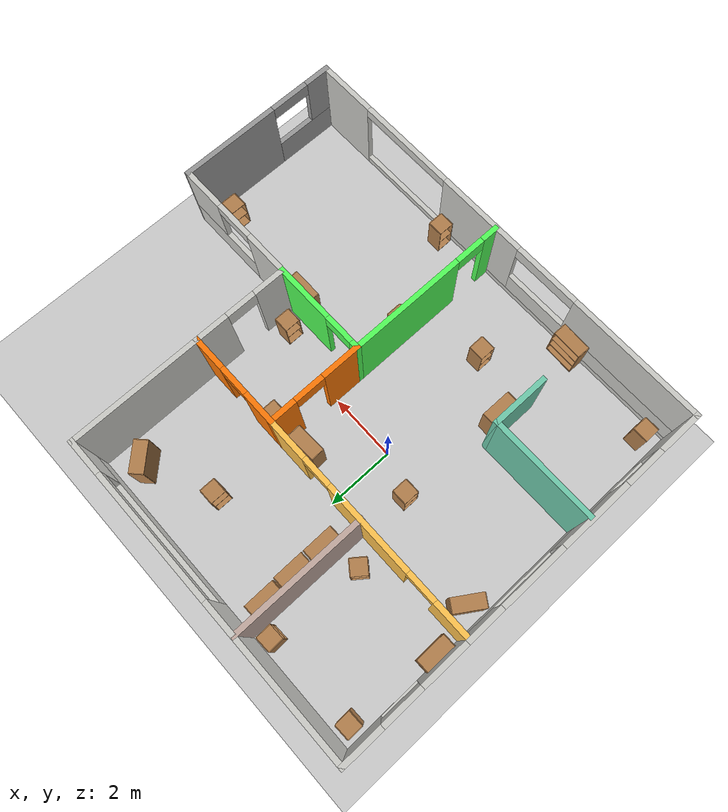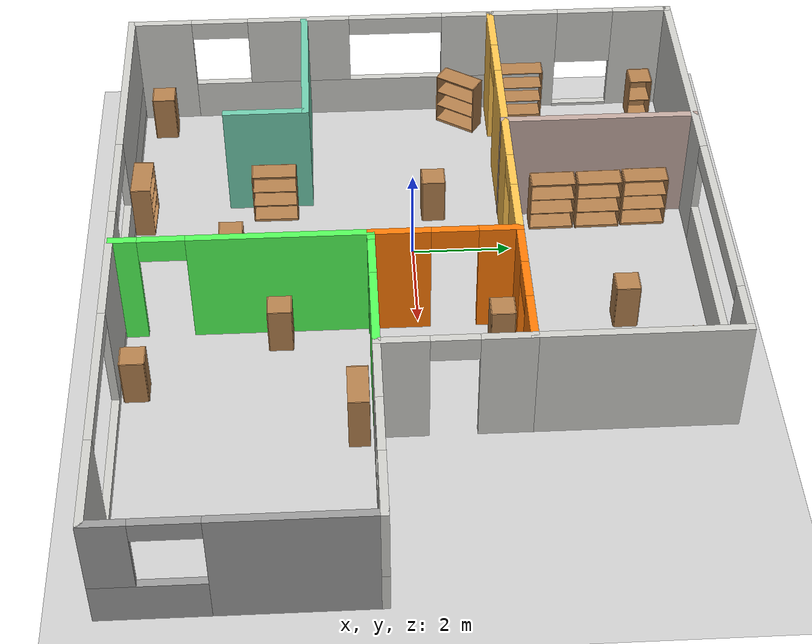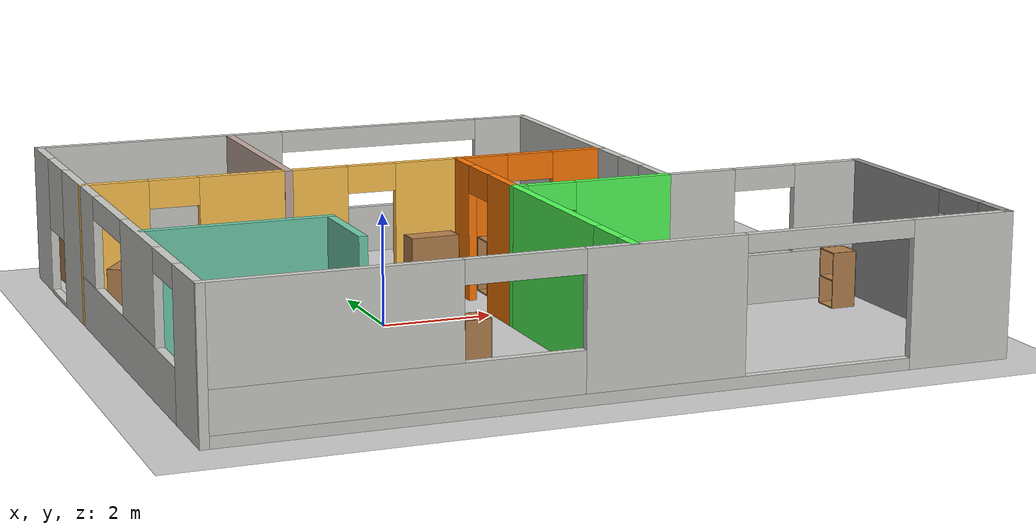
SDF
<sdf version="1.6">
 <world name="default">
  <plugin name="welcomemessage" filename="libwelcomemessage.so"/>
  <light name="sun" type="directional">
   <pose>0 0 10 0 -0 0</pose>
   <diffuse>0.8 0.8 0.8 1</diffuse>
   <specular>0.2 0.2 0.2 1</specular>
   <attenuation>
    <range>1000</range>
    <constant>0.9</constant>
    <linear>0.01</linear>
    <quadratic>0.001</quadratic>
   </attenuation>
   <direction>-0.5 0.1 -0.9</direction>
  </light>
  <model name="ground_plane">
   <static>1</static>
   <link name="link">
    <collision name="collision">
     <geometry><plane><normal>0 0 1</normal><size>100 100</size></plane></geometry>
     <surface>
      <contact><collide_bitmask>65535</collide_bitmask></contact>
      <friction><ode><mu>100</mu><mu2>50</mu2></ode></friction>
     </surface>
    </collision>
    <visual name="visual">
     <cast_shadows>0</cast_shadows>
     <geometry><plane><normal>0 0 1</normal><size>100 100</size></plane></geometry>
     <material>
      <script><uri>file://media/materials/scripts/gazebo.material</uri><name>Gazebo/Grey</name></script>
     </material>
    </visual>
   </link>
  </model>
  <gravity>0 0 -9.8</gravity>
  <magnetic_field>6e-06 2.3e-05 -4.2e-05</magnetic_field>
  <atmosphere type="adiabatic"/>
  <physics name="default_physics" default="0" type="ode">
   <max_step_size>0.001</max_step_size>
   <real_time_factor>1</real_time_factor>
   <real_time_update_rate>1000</real_time_update_rate>
  </physics>
  <scene><ambient>0.4 0.4 0.4 1</ambient><background>0.7 0.7 0.7 1</background><shadows>1</shadows></scene>
  <audio><device>default</device></audio>
  <spherical_coordinates>
   <surface_model>EARTH_WGS84</surface_model>
   <latitude_deg>0</latitude_deg>
   <longitude_deg>0</longitude_deg>
   <elevation>0</elevation>
   <heading_deg>0</heading_deg>
  </spherical_coordinates>
  <model name="Apartment">
   <pose>2.01045 -0.0125 0 0 -0 0</pose>
   <link name="Wall_11">
    <pose>1.52493 1.92485 0 0 -0 0</pose>
    <visual name="Wall_11_Visual_0">
     <pose>-0.9825 0 1.25 0 -0 0</pose>
     <geometry><box><size>1.035 0.15 2.5</size></box></geometry>
     <material>
      <script><uri>file://media/materials/scripts/gazebo.material</uri><name>Gazebo/Grey</name></script>
      <ambient>0.996078 0.47451 0.0196078 1</ambient>
     </material>
     <meta><layer>0</layer></meta>
    </visual>
    <collision name="Wall_11_Collision_0">
     <geometry><box><size>1.035 0.15 2.5</size></box></geometry>
     <pose>-0.9825 0 1.25 0 -0 0</pose>
    </collision>
    <visual name="Wall_11_Visual_1">
     <pose>0.9675 0 1.25 0 -0 0</pose>
     <geometry><box><size>1.065 0.15 2.5</size></box></geometry>
     <material>
      <script><uri>file://media/materials/scripts/gazebo.material</uri><name>Gazebo/Grey</name></script>
      <ambient>0.996078 0.47451 0.0196078 1</ambient>
     </material>
     <meta><layer>0</layer></meta>
    </visual>
    <collision name="Wall_11_Collision_1">
     <geometry><box><size>1.065 0.15 2.5</size></box></geometry>
     <pose>0.9675 0 1.25 0 -0 0</pose>
    </collision>
    <visual name="Wall_11_Visual_2">
     <pose>-0.015 0 2.25 0 -0 0</pose>
     <geometry><box><size>0.9 0.15 0.5</size></box></geometry>
     <material>
      <script><uri>file://media/materials/scripts/gazebo.material</uri><name>Gazebo/Grey</name></script>
      <ambient>0.996078 0.47451 0.0196078 1</ambient>
     </material>
     <meta><layer>0</layer></meta>
    </visual>
    <collision name="Wall_11_Collision_2">
     <geometry><box><size>0.9 0.15 0.5</size></box></geometry>
     <pose>-0.015 0 2.25 0 -0 0</pose>
    </collision>
   </link>
   <link name="Wall_12">
    <pose>2.94993 0.519847 0 0 0 -1.5708</pose>
    <visual name="Wall_12_Visual_0">
     <pose>-0.962535 0 1.25 0 -0 0</pose>
     <geometry><box><size>1.03493 0.15 2.5</size></box></geometry>
     <material>
      <script><uri>file://media/materials/scripts/gazebo.material</uri><name>Gazebo/CeilingTiled</name></script>
      <ambient>1 1 1 1</ambient>
     </material>
     <meta><layer>0</layer></meta>
    </visual>
    <collision name="Wall_12_Collision_0">
     <geometry><box><size>1.03493 0.15 2.5</size></box></geometry>
     <pose>-0.962535 0 1.25 0 -0 0</pose>
    </collision>
    <visual name="Wall_12_Visual_1">
     <pose>0.967465 0 1.25 0 -0 0</pose>
     <geometry><box><size>1.02507 0.15 2.5</size></box></geometry>
     <material>
      <script><uri>file://media/materials/scripts/gazebo.material</uri><name>Gazebo/CeilingTiled</name></script>
      <ambient>1 1 1 1</ambient>
     </material>
     <meta><layer>0</layer></meta>
    </visual>
    <collision name="Wall_12_Collision_1">
     <geometry><box><size>1.02507 0.15 2.5</size></box></geometry>
     <pose>0.967465 0 1.25 0 -0 0</pose>
    </collision>
    <visual name="Wall_12_Visual_2">
     <pose>0.00493 0 2.25 0 -0 0</pose>
     <geometry><box><size>0.9 0.15 0.5</size></box></geometry>
     <material>
      <script><uri>file://media/materials/scripts/gazebo.material</uri><name>Gazebo/CeilingTiled</name></script>
      <ambient>1 1 1 1</ambient>
     </material>
     <meta><layer>0</layer></meta>
    </visual>
    <collision name="Wall_12_Collision_2">
     <geometry><box><size>0.9 0.15 0.5</size></box></geometry>
     <pose>0.00493 0 2.25 0 -0 0</pose>
    </collision>
   </link>
   <link name="Wall_13">
    <pose>1.52493 -0.885153 0 0 -0 3.14159</pose>
    <visual name="Wall_13_Visual_0">
     <pose>-0.592536 0 1.25 0 -0 0</pose>
     <geometry><box><size>1.81507 0.15 2.5</size></box></geometry>
     <material>
      <script><uri>file://media/materials/scripts/gazebo.material</uri><name>Gazebo/Grey</name></script>
      <ambient>0.321569 1 0.345098 1</ambient>
     </material>
     <meta><layer>0</layer></meta>
    </visual>
    <collision name="Wall_13_Collision_0">
     <geometry><box><size>1.81507 0.15 2.5</size></box></geometry>
     <pose>-0.592536 0 1.25 0 -0 0</pose>
    </collision>
    <visual name="Wall_13_Visual_1">
     <pose>1.35754 0 1.25 0 -0 0</pose>
     <geometry><box><size>0.285073 0.15 2.5</size></box></geometry>
     <material>
      <script><uri>file://media/materials/scripts/gazebo.material</uri><name>Gazebo/Grey</name></script>
      <ambient>0.321569 1 0.345098 1</ambient>
     </material>
     <meta><layer>0</layer></meta>
    </visual>
    <collision name="Wall_13_Collision_1">
     <geometry><box><size>0.285073 0.15 2.5</size></box></geometry>
     <pose>1.35754 0 1.25 0 -0 0</pose>
    </collision>
    <visual name="Wall_13_Visual_2">
     <pose>0.765 0 2.25 0 -0 0</pose>
     <geometry><box><size>0.9 0.15 0.5</size></box></geometry>
     <material>
      <script><uri>file://media/materials/scripts/gazebo.material</uri><name>Gazebo/Grey</name></script>
      <ambient>0.321569 1 0.345098 1</ambient>
     </material>
     <meta><layer>0</layer></meta>
    </visual>
    <collision name="Wall_13_Collision_2">
     <geometry><box><size>0.9 0.15 0.5</size></box></geometry>
     <pose>0.765 0 2.25 0 -0 0</pose>
    </collision>
   </link>
   <link name="Wall_14">
    <pose>0.099928 0.519847 0 0 -0 1.5708</pose>
    <visual name="Wall_14_Visual_0">
     <pose>-0.8739 0 1.25 0 -0 0</pose>
     <geometry><box><size>1.21261 0.15 2.5</size></box></geometry>
     <material>
      <script><uri>file://media/materials/scripts/gazebo.material</uri><name>Gazebo/Grey</name></script>
      <ambient>0.996078 0.47451 0.0196078 1</ambient>
     </material>
     <meta><layer>0</layer></meta>
    </visual>
    <collision name="Wall_14_Collision_0">
     <geometry><box><size>1.21261 0.15 2.5</size></box></geometry>
     <pose>-0.8739 0 1.25 0 -0 0</pose>
    </collision>
    <visual name="Wall_14_Visual_1">
     <pose>1.0563 0 1.25 0 -0 0</pose>
     <geometry><box><size>0.847799 0.15 2.5</size></box></geometry>
     <material>
      <script><uri>file://media/materials/scripts/gazebo.material</uri><name>Gazebo/Grey</name></script>
      <ambient>0.996078 0.47451 0.0196078 1</ambient>
     </material>
     <meta><layer>0</layer></meta>
    </visual>
    <collision name="Wall_14_Collision_1">
     <geometry><box><size>0.847799 0.15 2.5</size></box></geometry>
     <pose>1.0563 0 1.25 0 -0 0</pose>
    </collision>
    <visual name="Wall_14_Visual_2">
     <pose>0.182404 0 2.25 0 -0 0</pose>
     <geometry><box><size>0.9 0.15 0.5</size></box></geometry>
     <material>
      <script><uri>file://media/materials/scripts/gazebo.material</uri><name>Gazebo/Grey</name></script>
      <ambient>0.996078 0.47451 0.0196078 1</ambient>
     </material>
     <meta><layer>0</layer></meta>
    </visual>
    <collision name="Wall_14_Collision_2">
     <geometry><box><size>0.9 0.15 0.5</size></box></geometry>
     <pose>0.182404 0 2.25 0 -0 0</pose>
    </collision>
   </link>
   <link name="Wall_16">
    <pose>4.87493 -0.885153 0 0 -0 0</pose>
    <visual name="Wall_16_Visual_0">
     <pose>-1.29069 0 1.25 0 -0 0</pose>
     <geometry><box><size>1.41862 0.15 2.5</size></box></geometry>
     <material>
      <script><uri>file://media/materials/scripts/gazebo.material</uri><name>Gazebo/CeilingTiled</name></script>
      <ambient>0.760784 0.662745 0.627451 1</ambient>
     </material>
     <meta><layer>0</layer></meta>
    </visual>
    <collision name="Wall_16_Collision_0">
     <geometry><box><size>1.41862 0.15 2.5</size></box></geometry>
     <pose>-1.29069 0 1.25 0 -0 0</pose>
    </collision>
    <visual name="Wall_16_Visual_1">
     <pose>0.709309 0 0.45 0 -0 0</pose>
     <geometry><box><size>2.58138 0.15 0.9</size></box></geometry>
     <material>
      <script><uri>file://media/materials/scripts/gazebo.material</uri><name>Gazebo/CeilingTiled</name></script>
      <ambient>0.760784 0.662745 0.627451 1</ambient>
     </material>
     <meta><layer>0</layer></meta>
    </visual>
    <collision name="Wall_16_Collision_1">
     <geometry><box><size>2.58138 0.15 0.9</size></box></geometry>
     <pose>0.709309 0 0.45 0 -0 0</pose>
    </collision>
    <visual name="Wall_16_Visual_2">
     <pose>1.30931 0 1.7 0 -0 0</pose>
     <geometry><box><size>1.38138 0.15 1.6</size></box></geometry>
     <material>
      <script><uri>file://media/materials/scripts/gazebo.material</uri><name>Gazebo/CeilingTiled</name></script>
      <ambient>0.760784 0.662745 0.627451 1</ambient>
     </material>
     <meta><layer>0</layer></meta>
    </visual>
    <collision name="Wall_16_Collision_2">
     <geometry><box><size>1.38138 0.15 1.6</size></box></geometry>
     <pose>1.30931 0 1.7 0 -0 0</pose>
    </collision>
    <visual name="Wall_16_Visual_3">
     <pose>0.018619 0 2.3 0 -0 0</pose>
     <geometry><box><size>1.2 0.15 0.4</size></box></geometry>
     <material>
      <script><uri>file://media/materials/scripts/gazebo.material</uri><name>Gazebo/CeilingTiled</name></script>
      <ambient>0.760784 0.662745 0.627451 1</ambient>
     </material>
     <meta><layer>0</layer></meta>
    </visual>
    <collision name="Wall_16_Collision_3">
     <geometry><box><size>1.2 0.15 0.4</size></box></geometry>
     <pose>0.018619 0 2.3 0 -0 0</pose>
    </collision>
   </link>
   <link name="Wall_18">
    <pose>6.80018 -3.33 0 0 0 -1.57069</pose>
    <visual name="Wall_18_Visual_0">
     <pose>-1.01487 0 1.25 0 -0 0</pose>
     <geometry><box><size>3.00995 0.15 2.5</size></box></geometry>
     <material>
      <script><uri>file://media/materials/scripts/gazebo.material</uri><name>Gazebo/Grey</name></script>
      <ambient>1 1 1 1</ambient>
     </material>
     <meta><layer>0</layer></meta>
    </visual>
    <collision name="Wall_18_Collision_0">
     <geometry><box><size>3.00995 0.15 2.5</size></box></geometry>
     <pose>-1.01487 0 1.25 0 -0 0</pose>
    </collision>
    <visual name="Wall_18_Visual_1">
     <pose>1.50497 0 0.45 0 -0 0</pose>
     <geometry><box><size>2.02974 0.15 0.9</size></box></geometry>
     <material>
      <script><uri>file://media/materials/scripts/gazebo.material</uri><name>Gazebo/Grey</name></script>
      <ambient>1 1 1 1</ambient>
     </material>
     <meta><layer>0</layer></meta>
    </visual>
    <collision name="Wall_18_Collision_1">
     <geometry><box><size>2.02974 0.15 0.9</size></box></geometry>
     <pose>1.50497 0 0.45 0 -0 0</pose>
    </collision>
    <visual name="Wall_18_Visual_2">
     <pose>2.10497 0 1.7 0 -0 0</pose>
     <geometry><box><size>0.829741 0.15 1.6</size></box></geometry>
     <material>
      <script><uri>file://media/materials/scripts/gazebo.material</uri><name>Gazebo/Grey</name></script>
      <ambient>1 1 1 1</ambient>
     </material>
     <meta><layer>0</layer></meta>
    </visual>
    <collision name="Wall_18_Collision_2">
     <geometry><box><size>0.829741 0.15 1.6</size></box></geometry>
     <pose>2.10497 0 1.7 0 -0 0</pose>
    </collision>
    <visual name="Wall_18_Visual_3">
     <pose>1.0901 0 2.3 0 -0 0</pose>
     <geometry><box><size>1.2 0.15 0.4</size></box></geometry>
     <material>
      <script><uri>file://media/materials/scripts/gazebo.material</uri><name>Gazebo/Grey</name></script>
      <ambient>1 1 1 1</ambient>
     </material>
     <meta><layer>0</layer></meta>
    </visual>
    <collision name="Wall_18_Collision_3">
     <geometry><box><size>1.2 0.15 0.4</size></box></geometry>
     <pose>1.0901 0 2.3 0 -0 0</pose>
    </collision>
   </link>
   <link name="Wall_19">
    <pose>0.000427 -5.77484 0 0 -0 3.14159</pose>
    <visual name="Wall_19_Visual_0">
     <pose>-5.94597 0 1.25 0 -0 0</pose>
     <geometry><box><size>1.85806 0.15 2.5</size></box></geometry>
     <material>
      <script><uri>file://media/materials/scripts/gazebo.material</uri><name>Gazebo/CeilingTiled</name></script>
      <ambient>1 1 1 1</ambient>
     </material>
     <meta><layer>0</layer></meta>
    </visual>
    <collision name="Wall_19_Collision_0">
     <geometry><box><size>1.85806 0.15 2.5</size></box></geometry>
     <pose>-5.94597 0 1.25 0 -0 0</pose>
    </collision>
    <visual name="Wall_19_Visual_1">
     <pose>0.929031 0 0.1 0 -0 0</pose>
     <geometry><box><size>11.8919 0.15 0.2</size></box></geometry>
     <material>
      <script><uri>file://media/materials/scripts/gazebo.material</uri><name>Gazebo/CeilingTiled</name></script>
      <ambient>1 1 1 1</ambient>
     </material>
     <meta><layer>0</layer></meta>
    </visual>
    <collision name="Wall_19_Collision_1">
     <geometry><box><size>11.8919 0.15 0.2</size></box></geometry>
     <pose>0.929031 0 0.1 0 -0 0</pose>
    </collision>
    <visual name="Wall_19_Visual_2">
     <pose>-0.643119 0 1.35 0 -0 0</pose>
     <geometry><box><size>2.74764 0.15 2.3</size></box></geometry>
     <material>
      <script><uri>file://media/materials/scripts/gazebo.material</uri><name>Gazebo/CeilingTiled</name></script>
      <ambient>1 1 1 1</ambient>
     </material>
     <meta><layer>0</layer></meta>
    </visual>
    <collision name="Wall_19_Collision_2">
     <geometry><box><size>2.74764 0.15 2.3</size></box></geometry>
     <pose>-0.643119 0 1.35 0 -0 0</pose>
    </collision>
    <visual name="Wall_19_Visual_3">
     <pose>3.80285 0 0.55 0 -0 0</pose>
     <geometry><box><size>6.1443 0.15 0.7</size></box></geometry>
     <material>
      <script><uri>file://media/materials/scripts/gazebo.material</uri><name>Gazebo/CeilingTiled</name></script>
      <ambient>1 1 1 1</ambient>
     </material>
     <meta><layer>0</layer></meta>
    </visual>
    <collision name="Wall_19_Collision_3">
     <geometry><box><size>6.1443 0.15 0.7</size></box></geometry>
     <pose>3.80285 0 0.55 0 -0 0</pose>
    </collision>
    <visual name="Wall_19_Visual_4">
     <pose>4.80285 0 1.7 0 -0 0</pose>
     <geometry><box><size>4.1443 0.15 1.6</size></box></geometry>
     <material>
      <script><uri>file://media/materials/scripts/gazebo.material</uri><name>Gazebo/CeilingTiled</name></script>
      <ambient>1 1 1 1</ambient>
     </material>
     <meta><layer>0</layer></meta>
    </visual>
    <collision name="Wall_19_Collision_4">
     <geometry><box><size>4.1443 0.15 1.6</size></box></geometry>
     <pose>4.80285 0 1.7 0 -0 0</pose>
    </collision>
    <visual name="Wall_19_Visual_5">
     <pose>1.7307 0 2.3 0 -0 0</pose>
     <geometry><box><size>2 0.15 0.4</size></box></geometry>
     <material>
      <script><uri>file://media/materials/scripts/gazebo.material</uri><name>Gazebo/CeilingTiled</name></script>
      <ambient>1 1 1 1</ambient>
     </material>
     <meta><layer>0</layer></meta>
    </visual>
    <collision name="Wall_19_Collision_5">
     <geometry><box><size>2 0.15 0.4</size></box></geometry>
     <pose>1.7307 0 2.3 0 -0 0</pose>
    </collision>
    <visual name="Wall_19_Visual_6">
     <pose>-3.51694 0 2.35 0 -0 0</pose>
     <geometry><box><size>3 0.15 0.3</size></box></geometry>
     <material>
      <script><uri>file://media/materials/scripts/gazebo.material</uri><name>Gazebo/CeilingTiled</name></script>
      <ambient>1 1 1 1</ambient>
     </material>
     <meta><layer>0</layer></meta>
    </visual>
    <collision name="Wall_19_Collision_6">
     <geometry><box><size>3 0.15 0.3</size></box></geometry>
     <pose>-3.51694 0 2.35 0 -0 0</pose>
    </collision>
   </link>
   <link name="Wall_20">
    <pose>-6.79982 -1.925 0 0 -0 1.57086</pose>
    <visual name="Wall_20_Visual_0">
     <pose>-3.25093 0 1.25 0 -0 0</pose>
     <geometry><box><size>1.34782 0.15 2.5</size></box></geometry>
     <material>
      <script><uri>file://media/materials/scripts/gazebo.material</uri><name>Gazebo/CeilingTiled</name></script>
      <ambient>1 1 1 1</ambient>
     </material>
     <meta><layer>0</layer></meta>
    </visual>
    <collision name="Wall_20_Collision_0">
     <geometry><box><size>1.34782 0.15 2.5</size></box></geometry>
     <pose>-3.25093 0 1.25 0 -0 0</pose>
    </collision>
    <visual name="Wall_20_Visual_1">
     <pose>0.67391 0 0.45 0 -0 0</pose>
     <geometry><box><size>6.50187 0.15 0.9</size></box></geometry>
     <material>
      <script><uri>file://media/materials/scripts/gazebo.material</uri><name>Gazebo/CeilingTiled</name></script>
      <ambient>1 1 1 1</ambient>
     </material>
     <meta><layer>0</layer></meta>
    </visual>
    <collision name="Wall_20_Collision_1">
     <geometry><box><size>6.50187 0.15 0.9</size></box></geometry>
     <pose>0.67391 0 0.45 0 -0 0</pose>
    </collision>
    <visual name="Wall_20_Visual_2">
     <pose>-0.288611 0 1.7 0 -0 0</pose>
     <geometry><box><size>2.17682 0.15 1.6</size></box></geometry>
     <material>
      <script><uri>file://media/materials/scripts/gazebo.material</uri><name>Gazebo/CeilingTiled</name></script>
      <ambient>1 1 1 1</ambient>
     </material>
     <meta><layer>0</layer></meta>
    </visual>
    <collision name="Wall_20_Collision_2">
     <geometry><box><size>2.17682 0.15 1.6</size></box></geometry>
     <pose>-0.288611 0 1.7 0 -0 0</pose>
    </collision>
    <visual name="Wall_20_Visual_3">
     <pose>3.36232 0 1.7 0 -0 0</pose>
     <geometry><box><size>1.12504 0.15 1.6</size></box></geometry>
     <material>
      <script><uri>file://media/materials/scripts/gazebo.material</uri><name>Gazebo/CeilingTiled</name></script>
      <ambient>1 1 1 1</ambient>
     </material>
     <meta><layer>0</layer></meta>
    </visual>
    <collision name="Wall_20_Collision_3">
     <geometry><box><size>1.12504 0.15 1.6</size></box></geometry>
     <pose>3.36232 0 1.7 0 -0 0</pose>
    </collision>
    <visual name="Wall_20_Visual_4">
     <pose>-1.97702 0 2.3 0 -0 0</pose>
     <geometry><box><size>1.2 0.15 0.4</size></box></geometry>
     <material>
      <script><uri>file://media/materials/scripts/gazebo.material</uri><name>Gazebo/CeilingTiled</name></script>
      <ambient>1 1 1 1</ambient>
     </material>
     <meta><layer>0</layer></meta>
    </visual>
    <collision name="Wall_20_Collision_4">
     <geometry><box><size>1.2 0.15 0.4</size></box></geometry>
     <pose>-1.97702 0 2.3 0 -0 0</pose>
    </collision>
    <visual name="Wall_20_Visual_5">
     <pose>1.7998 0 2.3 0 -0 0</pose>
     <geometry><box><size>2 0.15 0.4</size></box></geometry>
     <material>
      <script><uri>file://media/materials/scripts/gazebo.material</uri><name>Gazebo/CeilingTiled</name></script>
      <ambient>1 1 1 1</ambient>
     </material>
     <meta><layer>0</layer></meta>
    </visual>
    <collision name="Wall_20_Collision_5">
     <geometry><box><size>2 0.15 0.4</size></box></geometry>
     <pose>1.7998 0 2.3 0 -0 0</pose>
    </collision>
   </link>
   <link name="Wall_21">
    <pose>-3.35007 1.92485 0 0 -0 0</pose>
    <visual name="Wall_21_Visual_0">
     <pose>-2.92004 0 1.25 0 -0 0</pose>
     <geometry><box><size>1.21065 0.15 2.5</size></box></geometry>
     <material>
      <script><uri>file://media/materials/scripts/gazebo.material</uri><name>Gazebo/Grey</name></script>
      <ambient>1 0.764706 0.305882 1</ambient>
     </material>
     <meta><layer>0</layer></meta>
    </visual>
    <collision name="Wall_21_Collision_0">
     <geometry><box><size>1.21065 0.15 2.5</size></box></geometry>
     <pose>-2.92004 0 1.25 0 -0 0</pose>
    </collision>
    <visual name="Wall_21_Visual_1">
     <pose>-0.045749 0 1.25 0 -0 0</pose>
     <geometry><box><size>2.73793 0.15 2.5</size></box></geometry>
     <material>
      <script><uri>file://media/materials/scripts/gazebo.material</uri><name>Gazebo/Grey</name></script>
      <ambient>1 0.764706 0.305882 1</ambient>
     </material>
     <meta><layer>0</layer></meta>
    </visual>
    <collision name="Wall_21_Collision_1">
     <geometry><box><size>2.73793 0.15 2.5</size></box></geometry>
     <pose>-0.045749 0 1.25 0 -0 0</pose>
    </collision>
    <visual name="Wall_21_Visual_2">
     <pose>2.87429 0 1.25 0 -0 0</pose>
     <geometry><box><size>1.30214 0.15 2.5</size></box></geometry>
     <material>
      <script><uri>file://media/materials/scripts/gazebo.material</uri><name>Gazebo/Grey</name></script>
      <ambient>1 0.764706 0.305882 1</ambient>
     </material>
     <meta><layer>0</layer></meta>
    </visual>
    <collision name="Wall_21_Collision_2">
     <geometry><box><size>1.30214 0.15 2.5</size></box></geometry>
     <pose>2.87429 0 1.25 0 -0 0</pose>
    </collision>
    <visual name="Wall_21_Visual_3">
     <pose>-1.86471 0 2.25 0 -0 0</pose>
     <geometry><box><size>0.9 0.15 0.5</size></box></geometry>
     <material>
      <script><uri>file://media/materials/scripts/gazebo.material</uri><name>Gazebo/Grey</name></script>
      <ambient>1 0.764706 0.305882 1</ambient>
     </material>
     <meta><layer>0</layer></meta>
    </visual>
    <collision name="Wall_21_Collision_3">
     <geometry><box><size>0.9 0.15 0.5</size></box></geometry>
     <pose>-1.86471 0 2.25 0 -0 0</pose>
    </collision>
    <visual name="Wall_21_Visual_4">
     <pose>1.77322 0 2.25 0 -0 0</pose>
     <geometry><box><size>0.9 0.15 0.5</size></box></geometry>
     <material>
      <script><uri>file://media/materials/scripts/gazebo.material</uri><name>Gazebo/Grey</name></script>
      <ambient>1 0.764706 0.305882 1</ambient>
     </material>
     <meta><layer>0</layer></meta>
    </visual>
    <collision name="Wall_21_Collision_4">
     <geometry><box><size>0.9 0.15 0.5</size></box></geometry>
     <pose>1.77322 0 2.25 0 -0 0</pose>
    </collision>
   </link>
   <link name="Wall_23">
    <pose>-6.80007 3.84985 0 0 -0 1.5708</pose>
    <visual name="Wall_23_Visual_0">
     <pose>-1.23081 0 1.25 0 -0 0</pose>
     <geometry><box><size>1.53838 0.15 2.5</size></box></geometry>
     <material>
      <script><uri>file://media/materials/scripts/gazebo.material</uri><name>Gazebo/CeilingTiled</name></script>
      <ambient>1 1 1 1</ambient>
     </material>
     <meta><layer>0</layer></meta>
    </visual>
    <collision name="Wall_23_Collision_0">
     <geometry><box><size>1.53838 0.15 2.5</size></box></geometry>
     <pose>-1.23081 0 1.25 0 -0 0</pose>
    </collision>
    <visual name="Wall_23_Visual_1">
     <pose>1.36919 0 1.25 0 -0 0</pose>
     <geometry><box><size>1.26162 0.15 2.5</size></box></geometry>
     <material>
      <script><uri>file://media/materials/scripts/gazebo.material</uri><name>Gazebo/CeilingTiled</name></script>
      <ambient>1 1 1 1</ambient>
     </material>
     <meta><layer>0</layer></meta>
    </visual>
    <collision name="Wall_23_Collision_1">
     <geometry><box><size>1.26162 0.15 2.5</size></box></geometry>
     <pose>1.36919 0 1.25 0 -0 0</pose>
    </collision>
    <visual name="Wall_23_Visual_2">
     <pose>0.138378 0 0 0 -0 0</pose>
     <geometry><box><size>1.2 0.15 0.1</size></box></geometry>
     <material>
      <script><uri>file://media/materials/scripts/gazebo.material</uri><name>Gazebo/CeilingTiled</name></script>
      <ambient>1 1 1 1</ambient>
     </material>
     <meta><layer>0</layer></meta>
    </visual>
    <collision name="Wall_23_Collision_2">
     <geometry><box><size>1.2 0.15 0.1</size></box></geometry>
     <pose>0.138378 0 0 0 -0 0</pose>
    </collision>
    <visual name="Wall_23_Visual_3">
     <pose>0.138378 0 1.85 0 -0 0</pose>
     <geometry><box><size>1.2 0.15 1.3</size></box></geometry>
     <material>
      <script><uri>file://media/materials/scripts/gazebo.material</uri><name>Gazebo/CeilingTiled</name></script>
      <ambient>1 1 1 1</ambient>
     </material>
     <meta><layer>0</layer></meta>
    </visual>
    <collision name="Wall_23_Collision_3">
     <geometry><box><size>1.2 0.15 1.3</size></box></geometry>
     <pose>0.138378 0 1.85 0 -0 0</pose>
    </collision>
   </link>
   <link name="Wall_24">
    <pose>-1.92507 5.77485 0 0 -0 0</pose>
    <visual name="Wall_24_Visual_0">
     <pose>-2.56096 0 1.25 0 -0 0</pose>
     <geometry><box><size>4.77807 0.15 2.5</size></box></geometry>
     <material>
      <script><uri>file://media/materials/scripts/gazebo.material</uri><name>Gazebo/CeilingTiled</name></script>
      <ambient>1 1 1 1</ambient>
     </material>
     <meta><layer>0</layer></meta>
    </visual>
    <collision name="Wall_24_Collision_0">
     <geometry><box><size>4.77807 0.15 2.5</size></box></geometry>
     <pose>-2.56096 0 1.25 0 -0 0</pose>
    </collision>
    <visual name="Wall_24_Visual_1">
     <pose>2.38903 0 0.45 0 -0 0</pose>
     <geometry><box><size>5.12193 0.15 0.9</size></box></geometry>
     <material>
      <script><uri>file://media/materials/scripts/gazebo.material</uri><name>Gazebo/CeilingTiled</name></script>
      <ambient>1 1 1 1</ambient>
     </material>
     <meta><layer>0</layer></meta>
    </visual>
    <collision name="Wall_24_Collision_1">
     <geometry><box><size>5.12193 0.15 0.9</size></box></geometry>
     <pose>2.38903 0 0.45 0 -0 0</pose>
    </collision>
    <visual name="Wall_24_Visual_2">
     <pose>4.38903 0 1.7 0 -0 0</pose>
     <geometry><box><size>1.12193 0.15 1.6</size></box></geometry>
     <material>
      <script><uri>file://media/materials/scripts/gazebo.material</uri><name>Gazebo/CeilingTiled</name></script>
      <ambient>1 1 1 1</ambient>
     </material>
     <meta><layer>0</layer></meta>
    </visual>
    <collision name="Wall_24_Collision_2">
     <geometry><box><size>1.12193 0.15 1.6</size></box></geometry>
     <pose>4.38903 0 1.7 0 -0 0</pose>
    </collision>
    <visual name="Wall_24_Visual_3">
     <pose>1.82807 0 2.3 0 -0 0</pose>
     <geometry><box><size>4 0.15 0.4</size></box></geometry>
     <material>
      <script><uri>file://media/materials/scripts/gazebo.material</uri><name>Gazebo/CeilingTiled</name></script>
      <ambient>1 1 1 1</ambient>
     </material>
     <meta><layer>0</layer></meta>
    </visual>
    <collision name="Wall_24_Collision_3">
     <geometry><box><size>4 0.15 0.4</size></box></geometry>
     <pose>1.82807 0 2.3 0 -0 0</pose>
    </collision>
   </link>
   <link name="Wall_25">
    <collision name="Wall_25_Collision">
     <geometry><box><size>3.99969 0.15 2.5</size></box></geometry>
     <pose>0 0 1.25 0 -0 0</pose>
    </collision>
    <visual name="Wall_25_Visual">
     <pose>0 0 1.25 0 -0 0</pose>
     <geometry><box><size>3.99969 0.15 2.5</size></box></geometry>
     <material>
      <script><uri>file://media/materials/scripts/gazebo.material</uri><name>Gazebo/CeilingTiled</name></script>
      <ambient>1 1 1 1</ambient>
     </material>
     <meta><layer>0</layer></meta>
    </visual>
    <pose>2.94993 3.84985 0 0 0 -1.5708</pose>
   </link>
   <link name="Wall_27">
    <collision name="Wall_27_Collision">
     <geometry><box><size>4 0.15 2.5</size></box></geometry>
     <pose>0 0 1.25 0 -0 0</pose>
    </collision>
    <visual name="Wall_27_Visual">
     <pose>0 0 1.25 0 -0 0</pose>
     <geometry><box><size>4 0.15 2.5</size></box></geometry>
     <material>
      <script><uri>file://media/materials/scripts/gazebo.material</uri><name>Gazebo/Grey</name></script>
      <ambient>0.760784 0.662745 0.627451 1</ambient>
     </material>
     <meta><layer>0</layer></meta>
    </visual>
    <pose>-3.13347 3.83972 0 0 -0 1.5708</pose>
   </link>
   <link name="Wall_31">
    <pose>0.099928 -3.31015 0 0 0 -1.5708</pose>
    <visual name="Wall_31_Visual_0">
     <pose>-0.723829 0 1.25 0 -0 0</pose>
     <geometry><box><size>3.55234 0.15 2.5</size></box></geometry>
     <material>
      <script><uri>file://media/materials/scripts/gazebo.material</uri><name>Gazebo/Grey</name></script>
      <ambient>0.321569 1 0.345098 1</ambient>
     </material>
     <meta><layer>0</layer></meta>
    </visual>
    <collision name="Wall_31_Collision_0">
     <geometry><box><size>3.55234 0.15 2.5</size></box></geometry>
     <pose>-0.723829 0 1.25 0 -0 0</pose>
    </collision>
    <visual name="Wall_31_Visual_1">
     <pose>2.22617 0 1.25 0 -0 0</pose>
     <geometry><box><size>0.547658 0.15 2.5</size></box></geometry>
     <material>
      <script><uri>file://media/materials/scripts/gazebo.material</uri><name>Gazebo/Grey</name></script>
      <ambient>0.321569 1 0.345098 1</ambient>
     </material>
     <meta><layer>0</layer></meta>
    </visual>
    <collision name="Wall_31_Collision_1">
     <geometry><box><size>0.547658 0.15 2.5</size></box></geometry>
     <pose>2.22617 0 1.25 0 -0 0</pose>
    </collision>
    <visual name="Wall_31_Visual_2">
     <pose>1.50234 0 2.25 0 -0 0</pose>
     <geometry><box><size>0.9 0.15 0.5</size></box></geometry>
     <material>
      <script><uri>file://media/materials/scripts/gazebo.material</uri><name>Gazebo/Grey</name></script>
      <ambient>0.321569 1 0.345098 1</ambient>
     </material>
     <meta><layer>0</layer></meta>
    </visual>
    <collision name="Wall_31_Collision_2">
     <geometry><box><size>0.9 0.15 0.5</size></box></geometry>
     <pose>1.50234 0 2.25 0 -0 0</pose>
    </collision>
   </link>
   <link name="Wall_35">
    <collision name="Wall_35_Collision">
     <geometry><box><size>3.25 0.15 2.5</size></box></geometry>
     <pose>0 0 1.25 0 -0 0</pose>
    </collision>
    <visual name="Wall_35_Visual">
     <pose>0 0 1.25 0 -0 0</pose>
     <geometry><box><size>3.25 0.15 2.5</size></box></geometry>
     <material>
      <script><uri>file://media/materials/scripts/gazebo.material</uri><name>Gazebo/Grey</name></script>
      <ambient>0.435294 0.796078 0.67451 1</ambient>
     </material>
     <meta><layer>0</layer></meta>
    </visual>
    <pose>-5.17735 -2.08457 0 0 -0 0</pose>
   </link>
   <link name="Wall_36">
    <collision name="Wall_36_Collision">
     <geometry><box><size>1.75 0.15 2.5</size></box></geometry>
     <pose>0 0 1.25 0 -0 0</pose>
    </collision>
    <visual name="Wall_36_Visual">
     <pose>0 0 1.25 0 -0 0</pose>
     <geometry><box><size>1.75 0.15 2.5</size></box></geometry>
     <material>
      <script><uri>file://media/materials/scripts/gazebo.material</uri><name>Gazebo/Grey</name></script>
      <ambient>0.435294 0.796078 0.67451 1</ambient>
     </material>
     <meta><layer>0</layer></meta>
    </visual>
    <pose>-3.62735 -2.88457 0 0 0 -1.5708</pose>
   </link>
   <static>1</static>
  </model>
  <model name="bookshelf">
   <static>1</static>
   <link name="link">
    <inertial><mass>1</mass></inertial>
    <collision name="back">
     <pose>0 0.005 0.6 0 -0 0</pose>
     <geometry><box><size>0.9 0.01 1.2</size></box></geometry>
    </collision>
    <visual name="visual1">
     <pose>0 0.005 0.6 0 -0 0</pose>
     <geometry><box><size>0.9 0.01 1.2</size></box></geometry>
     <material>
      <script><uri>file://media/materials/scripts/gazebo.material</uri><name>Gazebo/Wood</name></script>
     </material>
    </visual>
    <collision name="left_side">
     <pose>0.45 -0.195 0.6 0 -0 0</pose>
     <geometry><box><size>0.02 0.4 1.2</size></box></geometry>
    </collision>
    <visual name="visual2">
     <pose>0.45 -0.195 0.6 0 -0 0</pose>
     <geometry><box><size>0.02 0.4 1.2</size></box></geometry>
     <material>
      <script><uri>file://media/materials/scripts/gazebo.material</uri><name>Gazebo/Wood</name></script>
     </material>
    </visual>
    <collision name="right_side">
     <pose>-0.45 -0.195 0.6 0 -0 0</pose>
     <geometry><box><size>0.02 0.4 1.2</size></box></geometry>
    </collision>
    <visual name="visual3">
     <pose>-0.45 -0.195 0.6 0 -0 0</pose>
     <geometry><box><size>0.02 0.4 1.2</size></box></geometry>
     <material>
      <script><uri>file://media/materials/scripts/gazebo.material</uri><name>Gazebo/Wood</name></script>
     </material>
    </visual>
    <collision name="bottom">
     <pose>0 -0.195 0.03 0 -0 0</pose>
     <geometry><box><size>0.88 0.4 0.06</size></box></geometry>
    </collision>
    <visual name="visual4">
     <pose>0 -0.195 0.03 0 -0 0</pose>
     <geometry><box><size>0.88 0.4 0.06</size></box></geometry>
     <material>
      <script><uri>file://media/materials/scripts/gazebo.material</uri><name>Gazebo/Wood</name></script>
     </material>
    </visual>
    <collision name="top">
     <pose>0 -0.195 1.19 0 -0 0</pose>
     <geometry><box><size>0.88 0.4 0.02</size></box></geometry>
    </collision>
    <visual name="visual5">
     <pose>0 -0.195 1.19 0 -0 0</pose>
     <geometry><box><size>0.88 0.4 0.02</size></box></geometry>
     <material>
      <script><uri>file://media/materials/scripts/gazebo.material</uri><name>Gazebo/Wood</name></script>
     </material>
    </visual>
    <collision name="low_shelf">
     <pose>0 -0.195 0.43 0 -0 0</pose>
     <geometry><box><size>0.88 0.4 0.02</size></box></geometry>
    </collision>
    <visual name="visual6">
     <pose>0 -0.195 0.43 0 -0 0</pose>
     <geometry><box><size>0.88 0.4 0.02</size></box></geometry>
     <material>
      <script><uri>file://media/materials/scripts/gazebo.material</uri><name>Gazebo/Wood</name></script>
     </material>
    </visual>
    <collision name="high_shelf">
     <pose>0 -0.195 0.8 0 -0 0</pose>
     <geometry><box><size>0.88 0.4 0.02</size></box></geometry>
    </collision>
    <visual name="visual7">
     <pose>0 -0.195 0.8 0 -0 0</pose>
     <geometry><box><size>0.88 0.4 0.02</size></box></geometry>
     <material>
      <script><uri>file://media/materials/scripts/gazebo.material</uri><name>Gazebo/Wood</name></script>
     </material>
    </visual>
   </link>
   <pose>4.78077 -1.0483 0 0 -0 0</pose>
  </model>
  <model name="bookshelf_clone">
   <static>1</static>
   <link name="link">
    <inertial><mass>1</mass></inertial>
    <collision name="back">
     <pose>0 0.005 0.6 0 -0 0</pose>
     <geometry><box><size>0.9 0.01 1.2</size></box></geometry>
    </collision>
    <visual name="visual1">
     <pose>0 0.005 0.6 0 -0 0</pose>
     <geometry><box><size>0.9 0.01 1.2</size></box></geometry>
     <material>
      <script><uri>file://media/materials/scripts/gazebo.material</uri><name>Gazebo/Wood</name></script>
     </material>
    </visual>
    <collision name="left_side">
     <pose>0.45 -0.195 0.6 0 -0 0</pose>
     <geometry><box><size>0.02 0.4 1.2</size></box></geometry>
    </collision>
    <visual name="visual2">
     <pose>0.45 -0.195 0.6 0 -0 0</pose>
     <geometry><box><size>0.02 0.4 1.2</size></box></geometry>
     <material>
      <script><uri>file://media/materials/scripts/gazebo.material</uri><name>Gazebo/Wood</name></script>
     </material>
    </visual>
    <collision name="right_side">
     <pose>-0.45 -0.195 0.6 0 -0 0</pose>
     <geometry><box><size>0.02 0.4 1.2</size></box></geometry>
    </collision>
    <visual name="visual3">
     <pose>-0.45 -0.195 0.6 0 -0 0</pose>
     <geometry><box><size>0.02 0.4 1.2</size></box></geometry>
     <material>
      <script><uri>file://media/materials/scripts/gazebo.material</uri><name>Gazebo/Wood</name></script>
     </material>
    </visual>
    <collision name="bottom">
     <pose>0 -0.195 0.03 0 -0 0</pose>
     <geometry><box><size>0.88 0.4 0.06</size></box></geometry>
    </collision>
    <visual name="visual4">
     <pose>0 -0.195 0.03 0 -0 0</pose>
     <geometry><box><size>0.88 0.4 0.06</size></box></geometry>
     <material>
      <script><uri>file://media/materials/scripts/gazebo.material</uri><name>Gazebo/Wood</name></script>
     </material>
    </visual>
    <collision name="top">
     <pose>0 -0.195 1.19 0 -0 0</pose>
     <geometry><box><size>0.88 0.4 0.02</size></box></geometry>
    </collision>
    <visual name="visual5">
     <pose>0 -0.195 1.19 0 -0 0</pose>
     <geometry><box><size>0.88 0.4 0.02</size></box></geometry>
     <material>
      <script><uri>file://media/materials/scripts/gazebo.material</uri><name>Gazebo/Wood</name></script>
     </material>
    </visual>
    <collision name="low_shelf">
     <pose>0 -0.195 0.43 0 -0 0</pose>
     <geometry><box><size>0.88 0.4 0.02</size></box></geometry>
    </collision>
    <visual name="visual6">
     <pose>0 -0.195 0.43 0 -0 0</pose>
     <geometry><box><size>0.88 0.4 0.02</size></box></geometry>
     <material>
      <script><uri>file://media/materials/scripts/gazebo.material</uri><name>Gazebo/Wood</name></script>
     </material>
    </visual>
    <collision name="high_shelf">
     <pose>0 -0.195 0.8 0 -0 0</pose>
     <geometry><box><size>0.88 0.4 0.02</size></box></geometry>
    </collision>
    <visual name="visual7">
     <pose>0 -0.195 0.8 0 -0 0</pose>
     <geometry><box><size>0.88 0.4 0.02</size></box></geometry>
     <material>
      <script><uri>file://media/materials/scripts/gazebo.material</uri><name>Gazebo/Wood</name></script>
     </material>
    </visual>
   </link>
   <pose>-0.990469 4.82539 0 0 -0 1.57948</pose>
  </model>
  <model name="bookshelf_clone_2">
   <static>1</static>
   <link name="link">
    <inertial><mass>1</mass></inertial>
    <collision name="back">
     <pose>0 0.005 0.6 0 -0 0</pose>
     <geometry><box><size>0.9 0.01 1.2</size></box></geometry>
    </collision>
    <visual name="visual1">
     <pose>0 0.005 0.6 0 -0 0</pose>
     <geometry><box><size>0.9 0.01 1.2</size></box></geometry>
     <material>
      <script><uri>file://media/materials/scripts/gazebo.material</uri><name>Gazebo/Wood</name></script>
     </material>
    </visual>
    <collision name="left_side">
     <pose>0.45 -0.195 0.6 0 -0 0</pose>
     <geometry><box><size>0.02 0.4 1.2</size></box></geometry>
    </collision>
    <visual name="visual2">
     <pose>0.45 -0.195 0.6 0 -0 0</pose>
     <geometry><box><size>0.02 0.4 1.2</size></box></geometry>
     <material>
      <script><uri>file://media/materials/scripts/gazebo.material</uri><name>Gazebo/Wood</name></script>
     </material>
    </visual>
    <collision name="right_side">
     <pose>-0.45 -0.195 0.6 0 -0 0</pose>
     <geometry><box><size>0.02 0.4 1.2</size></box></geometry>
    </collision>
    <visual name="visual3">
     <pose>-0.45 -0.195 0.6 0 -0 0</pose>
     <geometry><box><size>0.02 0.4 1.2</size></box></geometry>
     <material>
      <script><uri>file://media/materials/scripts/gazebo.material</uri><name>Gazebo/Wood</name></script>
     </material>
    </visual>
    <collision name="bottom">
     <pose>0 -0.195 0.03 0 -0 0</pose>
     <geometry><box><size>0.88 0.4 0.06</size></box></geometry>
    </collision>
    <visual name="visual4">
     <pose>0 -0.195 0.03 0 -0 0</pose>
     <geometry><box><size>0.88 0.4 0.06</size></box></geometry>
     <material>
      <script><uri>file://media/materials/scripts/gazebo.material</uri><name>Gazebo/Wood</name></script>
     </material>
    </visual>
    <collision name="top">
     <pose>0 -0.195 1.19 0 -0 0</pose>
     <geometry><box><size>0.88 0.4 0.02</size></box></geometry>
    </collision>
    <visual name="visual5">
     <pose>0 -0.195 1.19 0 -0 0</pose>
     <geometry><box><size>0.88 0.4 0.02</size></box></geometry>
     <material>
      <script><uri>file://media/materials/scripts/gazebo.material</uri><name>Gazebo/Wood</name></script>
     </material>
    </visual>
    <collision name="low_shelf">
     <pose>0 -0.195 0.43 0 -0 0</pose>
     <geometry><box><size>0.88 0.4 0.02</size></box></geometry>
    </collision>
    <visual name="visual6">
     <pose>0 -0.195 0.43 0 -0 0</pose>
     <geometry><box><size>0.88 0.4 0.02</size></box></geometry>
     <material>
      <script><uri>file://media/materials/scripts/gazebo.material</uri><name>Gazebo/Wood</name></script>
     </material>
    </visual>
    <collision name="high_shelf">
     <pose>0 -0.195 0.8 0 -0 0</pose>
     <geometry><box><size>0.88 0.4 0.02</size></box></geometry>
    </collision>
    <visual name="visual7">
     <pose>0 -0.195 0.8 0 -0 0</pose>
     <geometry><box><size>0.88 0.4 0.02</size></box></geometry>
     <material>
      <script><uri>file://media/materials/scripts/gazebo.material</uri><name>Gazebo/Wood</name></script>
     </material>
    </visual>
   </link>
   <pose>-1.24809 -5.69317 0 0 -0 3.11328</pose>
  </model>
  <model name="cabinet">
   <static>1</static>
   <link name="cabinet_bottom_plate">
    <inertial>
     <pose>0 0 -1 0 -0 0</pose>
     <inertia><ixx>2.05</ixx><ixy>0</ixy><ixz>0</ixz><iyy>2.05</iyy><iyz>0</iyz><izz>2.05</izz></inertia>
     <mass>25</mass>
    </inertial>
    <collision name="cabinet_bottom_plate_geom">
     <pose>0 0 0.01 0 -0 0</pose>
     <geometry><box><size>0.45 0.45 0.02</size></box></geometry>
    </collision>
    <visual name="cabinet_bottom_plate_geom_visual">
     <pose>0 0 0.01 0 -0 0</pose>
     <geometry><box><size>0.45 0.45 0.02</size></box></geometry>
     <material>
      <script><uri>file://media/materials/scripts/gazebo.material</uri><name>Gazebo/Wood</name></script>
     </material>
    </visual>
    <collision name="cabinet_bottom_plate_geom_cabinet_back_plate">
     <pose>0.235 0 0.51 0 -0 0</pose>
     <geometry><box><size>0.02 0.45 1.02</size></box></geometry>
    </collision>
    <visual name="cabinet_bottom_plate_geom_cabinet_back_plate_visual">
     <pose>0.235 0 0.51 0 -0 0</pose>
     <geometry><box><size>0.02 0.45 1.02</size></box></geometry>
     <material>
      <script><uri>file://media/materials/scripts/gazebo.material</uri><name>Gazebo/Wood</name></script>
     </material>
    </visual>
    <collision name="cabinet_bottom_plate_geom_cabinet_left_plate">
     <pose>0 0.235 0.51 0 -0 0</pose>
     <geometry><box><size>0.45 0.02 1.02</size></box></geometry>
    </collision>
    <visual name="cabinet_bottom_plate_geom_cabinet_left_plate_visual">
     <pose>0 0.235 0.51 0 -0 0</pose>
     <geometry><box><size>0.45 0.02 1.02</size></box></geometry>
     <material>
      <script><uri>file://media/materials/scripts/gazebo.material</uri><name>Gazebo/Wood</name></script>
     </material>
    </visual>
    <collision name="cabinet_bottom_plate_geom_cabinet_middle_plate">
     <pose>0 0 0.51 0 -0 0</pose>
     <geometry><box><size>0.45 0.45 0.02</size></box></geometry>
    </collision>
    <visual name="cabinet_bottom_plate_geom_cabinet_middle_plate_visual">
     <pose>0 0 0.51 0 -0 0</pose>
     <geometry><box><size>0.45 0.45 0.02</size></box></geometry>
     <material>
      <script><uri>file://media/materials/scripts/gazebo.material</uri><name>Gazebo/Wood</name></script>
     </material>
    </visual>
    <collision name="cabinet_bottom_plate_geom_cabinet_right_plate">
     <pose>0 -0.235 0.51 0 -0 0</pose>
     <geometry><box><size>0.45 0.02 1.02</size></box></geometry>
    </collision>
    <visual name="cabinet_bottom_plate_geom_cabinet_right_plate_visual">
     <pose>0 -0.235 0.51 0 -0 0</pose>
     <geometry><box><size>0.45 0.02 1.02</size></box></geometry>
     <material>
      <script><uri>file://media/materials/scripts/gazebo.material</uri><name>Gazebo/Wood</name></script>
     </material>
    </visual>
    <collision name="cabinet_bottom_plate_geom_cabinet_top_plate">
     <pose>0 0 1.01 0 -0 0</pose>
     <geometry><box><size>0.45 0.45 0.02</size></box></geometry>
    </collision>
    <visual name="cabinet_bottom_plate_geom_cabinet_top_plate_visual">
     <pose>0 0 1.01 0 -0 0</pose>
     <geometry><box><size>0.45 0.45 0.02</size></box></geometry>
     <material>
      <script><uri>file://media/materials/scripts/gazebo.material</uri><name>Gazebo/Wood</name></script>
     </material>
    </visual>
   </link>
   <pose>8.1117 -1.54587 -0.005029 0 -0 0</pose>
  </model>
  <model name="bookshelf_clone_3">
   <static>1</static>
   <link name="link">
    <inertial><mass>1</mass></inertial>
    <collision name="back">
     <pose>0 0.005 0.6 0 -0 0</pose>
     <geometry><box><size>0.9 0.01 1.2</size></box></geometry>
    </collision>
    <visual name="visual1">
     <pose>0 0.005 0.6 0 -0 0</pose>
     <geometry><box><size>0.9 0.01 1.2</size></box></geometry>
     <material>
      <script><uri>file://media/materials/scripts/gazebo.material</uri><name>Gazebo/Wood</name></script>
     </material>
    </visual>
    <collision name="left_side">
     <pose>0.45 -0.195 0.6 0 -0 0</pose>
     <geometry><box><size>0.02 0.4 1.2</size></box></geometry>
    </collision>
    <visual name="visual2">
     <pose>0.45 -0.195 0.6 0 -0 0</pose>
     <geometry><box><size>0.02 0.4 1.2</size></box></geometry>
     <material>
      <script><uri>file://media/materials/scripts/gazebo.material</uri><name>Gazebo/Wood</name></script>
     </material>
    </visual>
    <collision name="right_side">
     <pose>-0.45 -0.195 0.6 0 -0 0</pose>
     <geometry><box><size>0.02 0.4 1.2</size></box></geometry>
    </collision>
    <visual name="visual3">
     <pose>-0.45 -0.195 0.6 0 -0 0</pose>
     <geometry><box><size>0.02 0.4 1.2</size></box></geometry>
     <material>
      <script><uri>file://media/materials/scripts/gazebo.material</uri><name>Gazebo/Wood</name></script>
     </material>
    </visual>
    <collision name="bottom">
     <pose>0 -0.195 0.03 0 -0 0</pose>
     <geometry><box><size>0.88 0.4 0.06</size></box></geometry>
    </collision>
    <visual name="visual4">
     <pose>0 -0.195 0.03 0 -0 0</pose>
     <geometry><box><size>0.88 0.4 0.06</size></box></geometry>
     <material>
      <script><uri>file://media/materials/scripts/gazebo.material</uri><name>Gazebo/Wood</name></script>
     </material>
    </visual>
    <collision name="top">
     <pose>0 -0.195 1.19 0 -0 0</pose>
     <geometry><box><size>0.88 0.4 0.02</size></box></geometry>
    </collision>
    <visual name="visual5">
     <pose>0 -0.195 1.19 0 -0 0</pose>
     <geometry><box><size>0.88 0.4 0.02</size></box></geometry>
     <material>
      <script><uri>file://media/materials/scripts/gazebo.material</uri><name>Gazebo/Wood</name></script>
     </material>
    </visual>
    <collision name="low_shelf">
     <pose>0 -0.195 0.43 0 -0 0</pose>
     <geometry><box><size>0.88 0.4 0.02</size></box></geometry>
    </collision>
    <visual name="visual6">
     <pose>0 -0.195 0.43 0 -0 0</pose>
     <geometry><box><size>0.88 0.4 0.02</size></box></geometry>
     <material>
      <script><uri>file://media/materials/scripts/gazebo.material</uri><name>Gazebo/Wood</name></script>
     </material>
    </visual>
    <collision name="high_shelf">
     <pose>0 -0.195 0.8 0 -0 0</pose>
     <geometry><box><size>0.88 0.4 0.02</size></box></geometry>
    </collision>
    <visual name="visual7">
     <pose>0 -0.195 0.8 0 -0 0</pose>
     <geometry><box><size>0.88 0.4 0.02</size></box></geometry>
     <material>
      <script><uri>file://media/materials/scripts/gazebo.material</uri><name>Gazebo/Wood</name></script>
     </material>
    </visual>
   </link>
   <pose>-1.48553 -2.79449 0 0 -0 1.56323</pose>
  </model>
  <model name="cabinet_clone">
   <static>1</static>
   <link name="cabinet_bottom_plate">
    <inertial>
     <pose>0 0 -1 0 -0 0</pose>
     <inertia><ixx>2.05</ixx><ixy>0</ixy><ixz>0</ixz><iyy>2.05</iyy><iyz>0</iyz><izz>2.05</izz></inertia>
     <mass>25</mass>
    </inertial>
    <collision name="cabinet_bottom_plate_geom">
     <pose>0 0 0.01 0 -0 0</pose>
     <geometry><box><size>0.45 0.45 0.02</size></box></geometry>
    </collision>
    <visual name="cabinet_bottom_plate_geom_visual">
     <pose>0 0 0.01 0 -0 0</pose>
     <geometry><box><size>0.45 0.45 0.02</size></box></geometry>
     <material>
      <script><uri>file://media/materials/scripts/gazebo.material</uri><name>Gazebo/Wood</name></script>
     </material>
    </visual>
    <collision name="cabinet_bottom_plate_geom_cabinet_back_plate">
     <pose>0.235 0 0.51 0 -0 0</pose>
     <geometry><box><size>0.02 0.45 1.02</size></box></geometry>
    </collision>
    <visual name="cabinet_bottom_plate_geom_cabinet_back_plate_visual">
     <pose>0.235 0 0.51 0 -0 0</pose>
     <geometry><box><size>0.02 0.45 1.02</size></box></geometry>
     <material>
      <script><uri>file://media/materials/scripts/gazebo.material</uri><name>Gazebo/Wood</name></script>
     </material>
    </visual>
    <collision name="cabinet_bottom_plate_geom_cabinet_left_plate">
     <pose>0 0.235 0.51 0 -0 0</pose>
     <geometry><box><size>0.45 0.02 1.02</size></box></geometry>
    </collision>
    <visual name="cabinet_bottom_plate_geom_cabinet_left_plate_visual">
     <pose>0 0.235 0.51 0 -0 0</pose>
     <geometry><box><size>0.45 0.02 1.02</size></box></geometry>
     <material>
      <script><uri>file://media/materials/scripts/gazebo.material</uri><name>Gazebo/Wood</name></script>
     </material>
    </visual>
    <collision name="cabinet_bottom_plate_geom_cabinet_middle_plate">
     <pose>0 0 0.51 0 -0 0</pose>
     <geometry><box><size>0.45 0.45 0.02</size></box></geometry>
    </collision>
    <visual name="cabinet_bottom_plate_geom_cabinet_middle_plate_visual">
     <pose>0 0 0.51 0 -0 0</pose>
     <geometry><box><size>0.45 0.45 0.02</size></box></geometry>
     <material>
      <script><uri>file://media/materials/scripts/gazebo.material</uri><name>Gazebo/Wood</name></script>
     </material>
    </visual>
    <collision name="cabinet_bottom_plate_geom_cabinet_right_plate">
     <pose>0 -0.235 0.51 0 -0 0</pose>
     <geometry><box><size>0.45 0.02 1.02</size></box></geometry>
    </collision>
    <visual name="cabinet_bottom_plate_geom_cabinet_right_plate_visual">
     <pose>0 -0.235 0.51 0 -0 0</pose>
     <geometry><box><size>0.45 0.02 1.02</size></box></geometry>
     <material>
      <script><uri>file://media/materials/scripts/gazebo.material</uri><name>Gazebo/Wood</name></script>
     </material>
    </visual>
    <collision name="cabinet_bottom_plate_geom_cabinet_top_plate">
     <pose>0 0 1.01 0 -0 0</pose>
     <geometry><box><size>0.45 0.45 0.02</size></box></geometry>
    </collision>
    <visual name="cabinet_bottom_plate_geom_cabinet_top_plate_visual">
     <pose>0 0 1.01 0 -0 0</pose>
     <geometry><box><size>0.45 0.45 0.02</size></box></geometry>
     <material>
      <script><uri>file://media/materials/scripts/gazebo.material</uri><name>Gazebo/Wood</name></script>
     </material>
    </visual>
   </link>
   <pose>-4.30746 5.22093 0.043779 0 0 -3.11635</pose>
  </model>
  <model name="bookshelf_clone_clone">
   <static>1</static>
   <link name="link">
    <inertial><mass>1</mass></inertial>
    <collision name="back">
     <pose>0 0.005 0.6 0 -0 0</pose>
     <geometry><box><size>0.9 0.01 1.2</size></box></geometry>
    </collision>
    <visual name="visual1">
     <pose>0 0.005 0.6 0 -0 0</pose>
     <geometry><box><size>0.9 0.01 1.2</size></box></geometry>
     <material>
      <script><uri>file://media/materials/scripts/gazebo.material</uri><name>Gazebo/Wood</name></script>
     </material>
    </visual>
    <collision name="left_side">
     <pose>0.45 -0.195 0.6 0 -0 0</pose>
     <geometry><box><size>0.02 0.4 1.2</size></box></geometry>
    </collision>
    <visual name="visual2">
     <pose>0.45 -0.195 0.6 0 -0 0</pose>
     <geometry><box><size>0.02 0.4 1.2</size></box></geometry>
     <material>
      <script><uri>file://media/materials/scripts/gazebo.material</uri><name>Gazebo/Wood</name></script>
     </material>
    </visual>
    <collision name="right_side">
     <pose>-0.45 -0.195 0.6 0 -0 0</pose>
     <geometry><box><size>0.02 0.4 1.2</size></box></geometry>
    </collision>
    <visual name="visual3">
     <pose>-0.45 -0.195 0.6 0 -0 0</pose>
     <geometry><box><size>0.02 0.4 1.2</size></box></geometry>
     <material>
      <script><uri>file://media/materials/scripts/gazebo.material</uri><name>Gazebo/Wood</name></script>
     </material>
    </visual>
    <collision name="bottom">
     <pose>0 -0.195 0.03 0 -0 0</pose>
     <geometry><box><size>0.88 0.4 0.06</size></box></geometry>
    </collision>
    <visual name="visual4">
     <pose>0 -0.195 0.03 0 -0 0</pose>
     <geometry><box><size>0.88 0.4 0.06</size></box></geometry>
     <material>
      <script><uri>file://media/materials/scripts/gazebo.material</uri><name>Gazebo/Wood</name></script>
     </material>
    </visual>
    <collision name="top">
     <pose>0 -0.195 1.19 0 -0 0</pose>
     <geometry><box><size>0.88 0.4 0.02</size></box></geometry>
    </collision>
    <visual name="visual5">
     <pose>0 -0.195 1.19 0 -0 0</pose>
     <geometry><box><size>0.88 0.4 0.02</size></box></geometry>
     <material>
      <script><uri>file://media/materials/scripts/gazebo.material</uri><name>Gazebo/Wood</name></script>
     </material>
    </visual>
    <collision name="low_shelf">
     <pose>0 -0.195 0.43 0 -0 0</pose>
     <geometry><box><size>0.88 0.4 0.02</size></box></geometry>
    </collision>
    <visual name="visual6">
     <pose>0 -0.195 0.43 0 -0 0</pose>
     <geometry><box><size>0.88 0.4 0.02</size></box></geometry>
     <material>
      <script><uri>file://media/materials/scripts/gazebo.material</uri><name>Gazebo/Wood</name></script>
     </material>
    </visual>
    <collision name="high_shelf">
     <pose>0 -0.195 0.8 0 -0 0</pose>
     <geometry><box><size>0.88 0.4 0.02</size></box></geometry>
    </collision>
    <visual name="visual7">
     <pose>0 -0.195 0.8 0 -0 0</pose>
     <geometry><box><size>0.88 0.4 0.02</size></box></geometry>
     <material>
      <script><uri>file://media/materials/scripts/gazebo.material</uri><name>Gazebo/Wood</name></script>
     </material>
    </visual>
   </link>
   <pose>-0.957403 3.86885 0 0 -0 1.57948</pose>
  </model>
  <model name="bookshelf_clone_clone_0">
   <static>1</static>
   <link name="link">
    <inertial><mass>1</mass></inertial>
    <collision name="back">
     <pose>0 0.005 0.6 0 -0 0</pose>
     <geometry><box><size>0.9 0.01 1.2</size></box></geometry>
    </collision>
    <visual name="visual1">
     <pose>0 0.005 0.6 0 -0 0</pose>
     <geometry><box><size>0.9 0.01 1.2</size></box></geometry>
     <material>
      <script><uri>file://media/materials/scripts/gazebo.material</uri><name>Gazebo/Wood</name></script>
     </material>
    </visual>
    <collision name="left_side">
     <pose>0.45 -0.195 0.6 0 -0 0</pose>
     <geometry><box><size>0.02 0.4 1.2</size></box></geometry>
    </collision>
    <visual name="visual2">
     <pose>0.45 -0.195 0.6 0 -0 0</pose>
     <geometry><box><size>0.02 0.4 1.2</size></box></geometry>
     <material>
      <script><uri>file://media/materials/scripts/gazebo.material</uri><name>Gazebo/Wood</name></script>
     </material>
    </visual>
    <collision name="right_side">
     <pose>-0.45 -0.195 0.6 0 -0 0</pose>
     <geometry><box><size>0.02 0.4 1.2</size></box></geometry>
    </collision>
    <visual name="visual3">
     <pose>-0.45 -0.195 0.6 0 -0 0</pose>
     <geometry><box><size>0.02 0.4 1.2</size></box></geometry>
     <material>
      <script><uri>file://media/materials/scripts/gazebo.material</uri><name>Gazebo/Wood</name></script>
     </material>
    </visual>
    <collision name="bottom">
     <pose>0 -0.195 0.03 0 -0 0</pose>
     <geometry><box><size>0.88 0.4 0.06</size></box></geometry>
    </collision>
    <visual name="visual4">
     <pose>0 -0.195 0.03 0 -0 0</pose>
     <geometry><box><size>0.88 0.4 0.06</size></box></geometry>
     <material>
      <script><uri>file://media/materials/scripts/gazebo.material</uri><name>Gazebo/Wood</name></script>
     </material>
    </visual>
    <collision name="top">
     <pose>0 -0.195 1.19 0 -0 0</pose>
     <geometry><box><size>0.88 0.4 0.02</size></box></geometry>
    </collision>
    <visual name="visual5">
     <pose>0 -0.195 1.19 0 -0 0</pose>
     <geometry><box><size>0.88 0.4 0.02</size></box></geometry>
     <material>
      <script><uri>file://media/materials/scripts/gazebo.material</uri><name>Gazebo/Wood</name></script>
     </material>
    </visual>
    <collision name="low_shelf">
     <pose>0 -0.195 0.43 0 -0 0</pose>
     <geometry><box><size>0.88 0.4 0.02</size></box></geometry>
    </collision>
    <visual name="visual6">
     <pose>0 -0.195 0.43 0 -0 0</pose>
     <geometry><box><size>0.88 0.4 0.02</size></box></geometry>
     <material>
      <script><uri>file://media/materials/scripts/gazebo.material</uri><name>Gazebo/Wood</name></script>
     </material>
    </visual>
    <collision name="high_shelf">
     <pose>0 -0.195 0.8 0 -0 0</pose>
     <geometry><box><size>0.88 0.4 0.02</size></box></geometry>
    </collision>
    <visual name="visual7">
     <pose>0 -0.195 0.8 0 -0 0</pose>
     <geometry><box><size>0.88 0.4 0.02</size></box></geometry>
     <material>
      <script><uri>file://media/materials/scripts/gazebo.material</uri><name>Gazebo/Wood</name></script>
     </material>
    </visual>
   </link>
   <pose>-0.955662 2.91292 0 0 -0 1.57948</pose>
  </model>
  <model name="bookshelf_clone_clone_1">
   <static>1</static>
   <link name="link">
    <inertial><mass>1</mass></inertial>
    <collision name="back">
     <pose>0 0.005 0.6 0 -0 0</pose>
     <geometry><box><size>0.9 0.01 1.2</size></box></geometry>
    </collision>
    <visual name="visual1">
     <pose>0 0.005 0.6 0 -0 0</pose>
     <geometry><box><size>0.9 0.01 1.2</size></box></geometry>
     <material>
      <script><uri>file://media/materials/scripts/gazebo.material</uri><name>Gazebo/Wood</name></script>
     </material>
    </visual>
    <collision name="left_side">
     <pose>0.45 -0.195 0.6 0 -0 0</pose>
     <geometry><box><size>0.02 0.4 1.2</size></box></geometry>
    </collision>
    <visual name="visual2">
     <pose>0.45 -0.195 0.6 0 -0 0</pose>
     <geometry><box><size>0.02 0.4 1.2</size></box></geometry>
     <material>
      <script><uri>file://media/materials/scripts/gazebo.material</uri><name>Gazebo/Wood</name></script>
     </material>
    </visual>
    <collision name="right_side">
     <pose>-0.45 -0.195 0.6 0 -0 0</pose>
     <geometry><box><size>0.02 0.4 1.2</size></box></geometry>
    </collision>
    <visual name="visual3">
     <pose>-0.45 -0.195 0.6 0 -0 0</pose>
     <geometry><box><size>0.02 0.4 1.2</size></box></geometry>
     <material>
      <script><uri>file://media/materials/scripts/gazebo.material</uri><name>Gazebo/Wood</name></script>
     </material>
    </visual>
    <collision name="bottom">
     <pose>0 -0.195 0.03 0 -0 0</pose>
     <geometry><box><size>0.88 0.4 0.06</size></box></geometry>
    </collision>
    <visual name="visual4">
     <pose>0 -0.195 0.03 0 -0 0</pose>
     <geometry><box><size>0.88 0.4 0.06</size></box></geometry>
     <material>
      <script><uri>file://media/materials/scripts/gazebo.material</uri><name>Gazebo/Wood</name></script>
     </material>
    </visual>
    <collision name="top">
     <pose>0 -0.195 1.19 0 -0 0</pose>
     <geometry><box><size>0.88 0.4 0.02</size></box></geometry>
    </collision>
    <visual name="visual5">
     <pose>0 -0.195 1.19 0 -0 0</pose>
     <geometry><box><size>0.88 0.4 0.02</size></box></geometry>
     <material>
      <script><uri>file://media/materials/scripts/gazebo.material</uri><name>Gazebo/Wood</name></script>
     </material>
    </visual>
    <collision name="low_shelf">
     <pose>0 -0.195 0.43 0 -0 0</pose>
     <geometry><box><size>0.88 0.4 0.02</size></box></geometry>
    </collision>
    <visual name="visual6">
     <pose>0 -0.195 0.43 0 -0 0</pose>
     <geometry><box><size>0.88 0.4 0.02</size></box></geometry>
     <material>
      <script><uri>file://media/materials/scripts/gazebo.material</uri><name>Gazebo/Wood</name></script>
     </material>
    </visual>
    <collision name="high_shelf">
     <pose>0 -0.195 0.8 0 -0 0</pose>
     <geometry><box><size>0.88 0.4 0.02</size></box></geometry>
    </collision>
    <visual name="visual7">
     <pose>0 -0.195 0.8 0 -0 0</pose>
     <geometry><box><size>0.88 0.4 0.02</size></box></geometry>
     <material>
      <script><uri>file://media/materials/scripts/gazebo.material</uri><name>Gazebo/Wood</name></script>
     </material>
    </visual>
   </link>
   <pose>1.45803 1.32606 0 0 0 -3.10742</pose>
  </model>
  <model name="bookshelf_clone_clone_2">
   <static>1</static>
   <link name="link">
    <inertial><mass>1</mass></inertial>
    <collision name="back">
     <pose>0 0.005 0.6 0 -0 0</pose>
     <geometry><box><size>0.9 0.01 1.2</size></box></geometry>
    </collision>
    <visual name="visual1">
     <pose>0 0.005 0.6 0 -0 0</pose>
     <geometry><box><size>0.9 0.01 1.2</size></box></geometry>
     <material>
      <script><uri>file://media/materials/scripts/gazebo.material</uri><name>Gazebo/Wood</name></script>
     </material>
    </visual>
    <collision name="left_side">
     <pose>0.45 -0.195 0.6 0 -0 0</pose>
     <geometry><box><size>0.02 0.4 1.2</size></box></geometry>
    </collision>
    <visual name="visual2">
     <pose>0.45 -0.195 0.6 0 -0 0</pose>
     <geometry><box><size>0.02 0.4 1.2</size></box></geometry>
     <material>
      <script><uri>file://media/materials/scripts/gazebo.material</uri><name>Gazebo/Wood</name></script>
     </material>
    </visual>
    <collision name="right_side">
     <pose>-0.45 -0.195 0.6 0 -0 0</pose>
     <geometry><box><size>0.02 0.4 1.2</size></box></geometry>
    </collision>
    <visual name="visual3">
     <pose>-0.45 -0.195 0.6 0 -0 0</pose>
     <geometry><box><size>0.02 0.4 1.2</size></box></geometry>
     <material>
      <script><uri>file://media/materials/scripts/gazebo.material</uri><name>Gazebo/Wood</name></script>
     </material>
    </visual>
    <collision name="bottom">
     <pose>0 -0.195 0.03 0 -0 0</pose>
     <geometry><box><size>0.88 0.4 0.06</size></box></geometry>
    </collision>
    <visual name="visual4">
     <pose>0 -0.195 0.03 0 -0 0</pose>
     <geometry><box><size>0.88 0.4 0.06</size></box></geometry>
     <material>
      <script><uri>file://media/materials/scripts/gazebo.material</uri><name>Gazebo/Wood</name></script>
     </material>
    </visual>
    <collision name="top">
     <pose>0 -0.195 1.19 0 -0 0</pose>
     <geometry><box><size>0.88 0.4 0.02</size></box></geometry>
    </collision>
    <visual name="visual5">
     <pose>0 -0.195 1.19 0 -0 0</pose>
     <geometry><box><size>0.88 0.4 0.02</size></box></geometry>
     <material>
      <script><uri>file://media/materials/scripts/gazebo.material</uri><name>Gazebo/Wood</name></script>
     </material>
    </visual>
    <collision name="low_shelf">
     <pose>0 -0.195 0.43 0 -0 0</pose>
     <geometry><box><size>0.88 0.4 0.02</size></box></geometry>
    </collision>
    <visual name="visual6">
     <pose>0 -0.195 0.43 0 -0 0</pose>
     <geometry><box><size>0.88 0.4 0.02</size></box></geometry>
     <material>
      <script><uri>file://media/materials/scripts/gazebo.material</uri><name>Gazebo/Wood</name></script>
     </material>
    </visual>
    <collision name="high_shelf">
     <pose>0 -0.195 0.8 0 -0 0</pose>
     <geometry><box><size>0.88 0.4 0.02</size></box></geometry>
    </collision>
    <visual name="visual7">
     <pose>0 -0.195 0.8 0 -0 0</pose>
     <geometry><box><size>0.88 0.4 0.02</size></box></geometry>
     <material>
      <script><uri>file://media/materials/scripts/gazebo.material</uri><name>Gazebo/Wood</name></script>
     </material>
    </visual>
   </link>
   <pose>-4.72678 2.62015 0 0 -0 1.57948</pose>
  </model>
  <model name="cabinet_clone_clone">
   <static>1</static>
   <link name="cabinet_bottom_plate">
    <inertial>
     <pose>0 0 -1 0 -0 0</pose>
     <inertia><ixx>2.05</ixx><ixy>0</ixy><ixz>0</ixz><iyy>2.05</iyy><iyz>0</iyz><izz>2.05</izz></inertia>
     <mass>25</mass>
    </inertial>
    <collision name="cabinet_bottom_plate_geom">
     <pose>0 0 0.01 0 -0 0</pose>
     <geometry><box><size>0.45 0.45 0.02</size></box></geometry>
    </collision>
    <visual name="cabinet_bottom_plate_geom_visual">
     <pose>0 0 0.01 0 -0 0</pose>
     <geometry><box><size>0.45 0.45 0.02</size></box></geometry>
     <material>
      <script><uri>file://media/materials/scripts/gazebo.material</uri><name>Gazebo/Wood</name></script>
     </material>
    </visual>
    <collision name="cabinet_bottom_plate_geom_cabinet_back_plate">
     <pose>0.235 0 0.51 0 -0 0</pose>
     <geometry><box><size>0.02 0.45 1.02</size></box></geometry>
    </collision>
    <visual name="cabinet_bottom_plate_geom_cabinet_back_plate_visual">
     <pose>0.235 0 0.51 0 -0 0</pose>
     <geometry><box><size>0.02 0.45 1.02</size></box></geometry>
     <material>
      <script><uri>file://media/materials/scripts/gazebo.material</uri><name>Gazebo/Wood</name></script>
     </material>
    </visual>
    <collision name="cabinet_bottom_plate_geom_cabinet_left_plate">
     <pose>0 0.235 0.51 0 -0 0</pose>
     <geometry><box><size>0.45 0.02 1.02</size></box></geometry>
    </collision>
    <visual name="cabinet_bottom_plate_geom_cabinet_left_plate_visual">
     <pose>0 0.235 0.51 0 -0 0</pose>
     <geometry><box><size>0.45 0.02 1.02</size></box></geometry>
     <material>
      <script><uri>file://media/materials/scripts/gazebo.material</uri><name>Gazebo/Wood</name></script>
     </material>
    </visual>
    <collision name="cabinet_bottom_plate_geom_cabinet_middle_plate">
     <pose>0 0 0.51 0 -0 0</pose>
     <geometry><box><size>0.45 0.45 0.02</size></box></geometry>
    </collision>
    <visual name="cabinet_bottom_plate_geom_cabinet_middle_plate_visual">
     <pose>0 0 0.51 0 -0 0</pose>
     <geometry><box><size>0.45 0.45 0.02</size></box></geometry>
     <material>
      <script><uri>file://media/materials/scripts/gazebo.material</uri><name>Gazebo/Wood</name></script>
     </material>
    </visual>
    <collision name="cabinet_bottom_plate_geom_cabinet_right_plate">
     <pose>0 -0.235 0.51 0 -0 0</pose>
     <geometry><box><size>0.45 0.02 1.02</size></box></geometry>
    </collision>
    <visual name="cabinet_bottom_plate_geom_cabinet_right_plate_visual">
     <pose>0 -0.235 0.51 0 -0 0</pose>
     <geometry><box><size>0.45 0.02 1.02</size></box></geometry>
     <material>
      <script><uri>file://media/materials/scripts/gazebo.material</uri><name>Gazebo/Wood</name></script>
     </material>
    </visual>
    <collision name="cabinet_bottom_plate_geom_cabinet_top_plate">
     <pose>0 0 1.01 0 -0 0</pose>
     <geometry><box><size>0.45 0.45 0.02</size></box></geometry>
    </collision>
    <visual name="cabinet_bottom_plate_geom_cabinet_top_plate_visual">
     <pose>0 0 1.01 0 -0 0</pose>
     <geometry><box><size>0.45 0.45 0.02</size></box></geometry>
     <material>
      <script><uri>file://media/materials/scripts/gazebo.material</uri><name>Gazebo/Wood</name></script>
     </material>
    </visual>
   </link>
   <pose>-1.5796 5.30586 0.15688 0 -0 1.6015</pose>
  </model>
  <plugin name="collision_map_creator" filename="libcollision_map_creator.so"/>
  <model name="cabinet_clone_0">
   <static>1</static>
   <link name="cabinet_bottom_plate">
    <inertial>
     <pose>0 0 -1 0 -0 0</pose>
     <inertia><ixx>2.05</ixx><ixy>0</ixy><ixz>0</ixz><iyy>2.05</iyy><iyz>0</iyz><izz>2.05</izz></inertia>
     <mass>25</mass>
    </inertial>
    <collision name="cabinet_bottom_plate_geom">
     <pose>0 0 0.01 0 -0 0</pose>
     <geometry><box><size>0.45 0.45 0.02</size></box></geometry>
    </collision>
    <visual name="cabinet_bottom_plate_geom_visual">
     <pose>0 0 0.01 0 -0 0</pose>
     <geometry><box><size>0.45 0.45 0.02</size></box></geometry>
     <material>
      <script><uri>file://media/materials/scripts/gazebo.material</uri><name>Gazebo/Wood</name></script>
     </material>
    </visual>
    <collision name="cabinet_bottom_plate_geom_cabinet_back_plate">
     <pose>0.235 0 0.51 0 -0 0</pose>
     <geometry><box><size>0.02 0.45 1.02</size></box></geometry>
    </collision>
    <visual name="cabinet_bottom_plate_geom_cabinet_back_plate_visual">
     <pose>0.235 0 0.51 0 -0 0</pose>
     <geometry><box><size>0.02 0.45 1.02</size></box></geometry>
     <material>
      <script><uri>file://media/materials/scripts/gazebo.material</uri><name>Gazebo/Wood</name></script>
     </material>
    </visual>
    <collision name="cabinet_bottom_plate_geom_cabinet_left_plate">
     <pose>0 0.235 0.51 0 -0 0</pose>
     <geometry><box><size>0.45 0.02 1.02</size></box></geometry>
    </collision>
    <visual name="cabinet_bottom_plate_geom_cabinet_left_plate_visual">
     <pose>0 0.235 0.51 0 -0 0</pose>
     <geometry><box><size>0.45 0.02 1.02</size></box></geometry>
     <material>
      <script><uri>file://media/materials/scripts/gazebo.material</uri><name>Gazebo/Wood</name></script>
     </material>
    </visual>
    <collision name="cabinet_bottom_plate_geom_cabinet_middle_plate">
     <pose>0 0 0.51 0 -0 0</pose>
     <geometry><box><size>0.45 0.45 0.02</size></box></geometry>
    </collision>
    <visual name="cabinet_bottom_plate_geom_cabinet_middle_plate_visual">
     <pose>0 0 0.51 0 -0 0</pose>
     <geometry><box><size>0.45 0.45 0.02</size></box></geometry>
     <material>
      <script><uri>file://media/materials/scripts/gazebo.material</uri><name>Gazebo/Wood</name></script>
     </material>
    </visual>
    <collision name="cabinet_bottom_plate_geom_cabinet_right_plate">
     <pose>0 -0.235 0.51 0 -0 0</pose>
     <geometry><box><size>0.45 0.02 1.02</size></box></geometry>
    </collision>
    <visual name="cabinet_bottom_plate_geom_cabinet_right_plate_visual">
     <pose>0 -0.235 0.51 0 -0 0</pose>
     <geometry><box><size>0.45 0.02 1.02</size></box></geometry>
     <material>
      <script><uri>file://media/materials/scripts/gazebo.material</uri><name>Gazebo/Wood</name></script>
     </material>
    </visual>
    <collision name="cabinet_bottom_plate_geom_cabinet_top_plate">
     <pose>0 0 1.01 0 -0 0</pose>
     <geometry><box><size>0.45 0.45 0.02</size></box></geometry>
    </collision>
    <visual name="cabinet_bottom_plate_geom_cabinet_top_plate_visual">
     <pose>0 0 1.01 0 -0 0</pose>
     <geometry><box><size>0.45 0.45 0.02</size></box></geometry>
     <material>
      <script><uri>file://media/materials/scripts/gazebo.material</uri><name>Gazebo/Wood</name></script>
     </material>
    </visual>
   </link>
   <pose>4.3942 -0.360163 -0.005029 0 -0 0</pose>
  </model>
  <model name="cabinet_clone_1">
   <static>1</static>
   <link name="cabinet_bottom_plate">
    <inertial>
     <pose>0 0 -1 0 -0 0</pose>
     <inertia><ixx>2.05</ixx><ixy>0</ixy><ixz>0</ixz><iyy>2.05</iyy><iyz>0</iyz><izz>2.05</izz></inertia>
     <mass>25</mass>
    </inertial>
    <collision name="cabinet_bottom_plate_geom">
     <pose>0 0 0.01 0 -0 0</pose>
     <geometry><box><size>0.45 0.45 0.02</size></box></geometry>
    </collision>
    <visual name="cabinet_bottom_plate_geom_visual">
     <pose>0 0 0.01 0 -0 0</pose>
     <geometry><box><size>0.45 0.45 0.02</size></box></geometry>
     <material>
      <script><uri>file://media/materials/scripts/gazebo.material</uri><name>Gazebo/Wood</name></script>
     </material>
    </visual>
    <collision name="cabinet_bottom_plate_geom_cabinet_back_plate">
     <pose>0.235 0 0.51 0 -0 0</pose>
     <geometry><box><size>0.02 0.45 1.02</size></box></geometry>
    </collision>
    <visual name="cabinet_bottom_plate_geom_cabinet_back_plate_visual">
     <pose>0.235 0 0.51 0 -0 0</pose>
     <geometry><box><size>0.02 0.45 1.02</size></box></geometry>
     <material>
      <script><uri>file://media/materials/scripts/gazebo.material</uri><name>Gazebo/Wood</name></script>
     </material>
    </visual>
    <collision name="cabinet_bottom_plate_geom_cabinet_left_plate">
     <pose>0 0.235 0.51 0 -0 0</pose>
     <geometry><box><size>0.45 0.02 1.02</size></box></geometry>
    </collision>
    <visual name="cabinet_bottom_plate_geom_cabinet_left_plate_visual">
     <pose>0 0.235 0.51 0 -0 0</pose>
     <geometry><box><size>0.45 0.02 1.02</size></box></geometry>
     <material>
      <script><uri>file://media/materials/scripts/gazebo.material</uri><name>Gazebo/Wood</name></script>
     </material>
    </visual>
    <collision name="cabinet_bottom_plate_geom_cabinet_middle_plate">
     <pose>0 0 0.51 0 -0 0</pose>
     <geometry><box><size>0.45 0.45 0.02</size></box></geometry>
    </collision>
    <visual name="cabinet_bottom_plate_geom_cabinet_middle_plate_visual">
     <pose>0 0 0.51 0 -0 0</pose>
     <geometry><box><size>0.45 0.45 0.02</size></box></geometry>
     <material>
      <script><uri>file://media/materials/scripts/gazebo.material</uri><name>Gazebo/Wood</name></script>
     </material>
    </visual>
    <collision name="cabinet_bottom_plate_geom_cabinet_right_plate">
     <pose>0 -0.235 0.51 0 -0 0</pose>
     <geometry><box><size>0.45 0.02 1.02</size></box></geometry>
    </collision>
    <visual name="cabinet_bottom_plate_geom_cabinet_right_plate_visual">
     <pose>0 -0.235 0.51 0 -0 0</pose>
     <geometry><box><size>0.45 0.02 1.02</size></box></geometry>
     <material>
      <script><uri>file://media/materials/scripts/gazebo.material</uri><name>Gazebo/Wood</name></script>
     </material>
    </visual>
    <collision name="cabinet_bottom_plate_geom_cabinet_top_plate">
     <pose>0 0 1.01 0 -0 0</pose>
     <geometry><box><size>0.45 0.45 0.02</size></box></geometry>
    </collision>
    <visual name="cabinet_bottom_plate_geom_cabinet_top_plate_visual">
     <pose>0 0 1.01 0 -0 0</pose>
     <geometry><box><size>0.45 0.45 0.02</size></box></geometry>
     <material>
      <script><uri>file://media/materials/scripts/gazebo.material</uri><name>Gazebo/Wood</name></script>
     </material>
    </visual>
   </link>
   <pose>2.69652 1.59159 -0.005029 0 -0 0</pose>
  </model>
  <model name="cabinet_clone_2">
   <static>1</static>
   <link name="cabinet_bottom_plate">
    <inertial>
     <pose>0 0 -1 0 -0 0</pose>
     <inertia><ixx>2.05</ixx><ixy>0</ixy><ixz>0</ixz><iyy>2.05</iyy><iyz>0</iyz><izz>2.05</izz></inertia>
     <mass>25</mass>
    </inertial>
    <collision name="cabinet_bottom_plate_geom">
     <pose>0 0 0.01 0 -0 0</pose>
     <geometry><box><size>0.45 0.45 0.02</size></box></geometry>
    </collision>
    <visual name="cabinet_bottom_plate_geom_visual">
     <pose>0 0 0.01 0 -0 0</pose>
     <geometry><box><size>0.45 0.45 0.02</size></box></geometry>
     <material>
      <script><uri>file://media/materials/scripts/gazebo.material</uri><name>Gazebo/Wood</name></script>
     </material>
    </visual>
    <collision name="cabinet_bottom_plate_geom_cabinet_back_plate">
     <pose>0.235 0 0.51 0 -0 0</pose>
     <geometry><box><size>0.02 0.45 1.02</size></box></geometry>
    </collision>
    <visual name="cabinet_bottom_plate_geom_cabinet_back_plate_visual">
     <pose>0.235 0 0.51 0 -0 0</pose>
     <geometry><box><size>0.02 0.45 1.02</size></box></geometry>
     <material>
      <script><uri>file://media/materials/scripts/gazebo.material</uri><name>Gazebo/Wood</name></script>
     </material>
    </visual>
    <collision name="cabinet_bottom_plate_geom_cabinet_left_plate">
     <pose>0 0.235 0.51 0 -0 0</pose>
     <geometry><box><size>0.45 0.02 1.02</size></box></geometry>
    </collision>
    <visual name="cabinet_bottom_plate_geom_cabinet_left_plate_visual">
     <pose>0 0.235 0.51 0 -0 0</pose>
     <geometry><box><size>0.45 0.02 1.02</size></box></geometry>
     <material>
      <script><uri>file://media/materials/scripts/gazebo.material</uri><name>Gazebo/Wood</name></script>
     </material>
    </visual>
    <collision name="cabinet_bottom_plate_geom_cabinet_middle_plate">
     <pose>0 0 0.51 0 -0 0</pose>
     <geometry><box><size>0.45 0.45 0.02</size></box></geometry>
    </collision>
    <visual name="cabinet_bottom_plate_geom_cabinet_middle_plate_visual">
     <pose>0 0 0.51 0 -0 0</pose>
     <geometry><box><size>0.45 0.45 0.02</size></box></geometry>
     <material>
      <script><uri>file://media/materials/scripts/gazebo.material</uri><name>Gazebo/Wood</name></script>
     </material>
    </visual>
    <collision name="cabinet_bottom_plate_geom_cabinet_right_plate">
     <pose>0 -0.235 0.51 0 -0 0</pose>
     <geometry><box><size>0.45 0.02 1.02</size></box></geometry>
    </collision>
    <visual name="cabinet_bottom_plate_geom_cabinet_right_plate_visual">
     <pose>0 -0.235 0.51 0 -0 0</pose>
     <geometry><box><size>0.45 0.02 1.02</size></box></geometry>
     <material>
      <script><uri>file://media/materials/scripts/gazebo.material</uri><name>Gazebo/Wood</name></script>
     </material>
    </visual>
    <collision name="cabinet_bottom_plate_geom_cabinet_top_plate">
     <pose>0 0 1.01 0 -0 0</pose>
     <geometry><box><size>0.45 0.45 0.02</size></box></geometry>
    </collision>
    <visual name="cabinet_bottom_plate_geom_cabinet_top_plate_visual">
     <pose>0 0 1.01 0 -0 0</pose>
     <geometry><box><size>0.45 0.45 0.02</size></box></geometry>
     <material>
      <script><uri>file://media/materials/scripts/gazebo.material</uri><name>Gazebo/Wood</name></script>
     </material>
    </visual>
   </link>
   <pose>3.67164 -5.4175 -0.005029 0 -0 0</pose>
  </model>
  <model name="cabinet_clone_3">
   <static>1</static>
   <link name="cabinet_bottom_plate">
    <inertial>
     <pose>0 0 -1 0 -0 0</pose>
     <inertia><ixx>2.05</ixx><ixy>0</ixy><ixz>0</ixz><iyy>2.05</iyy><iyz>0</iyz><izz>2.05</izz></inertia>
     <mass>25</mass>
    </inertial>
    <collision name="cabinet_bottom_plate_geom">
     <pose>0 0 0.01 0 -0 0</pose>
     <geometry><box><size>0.45 0.45 0.02</size></box></geometry>
    </collision>
    <visual name="cabinet_bottom_plate_geom_visual">
     <pose>0 0 0.01 0 -0 0</pose>
     <geometry><box><size>0.45 0.45 0.02</size></box></geometry>
     <material>
      <script><uri>file://media/materials/scripts/gazebo.material</uri><name>Gazebo/Wood</name></script>
     </material>
    </visual>
    <collision name="cabinet_bottom_plate_geom_cabinet_back_plate">
     <pose>0.235 0 0.51 0 -0 0</pose>
     <geometry><box><size>0.02 0.45 1.02</size></box></geometry>
    </collision>
    <visual name="cabinet_bottom_plate_geom_cabinet_back_plate_visual">
     <pose>0.235 0 0.51 0 -0 0</pose>
     <geometry><box><size>0.02 0.45 1.02</size></box></geometry>
     <material>
      <script><uri>file://media/materials/scripts/gazebo.material</uri><name>Gazebo/Wood</name></script>
     </material>
    </visual>
    <collision name="cabinet_bottom_plate_geom_cabinet_left_plate">
     <pose>0 0.235 0.51 0 -0 0</pose>
     <geometry><box><size>0.45 0.02 1.02</size></box></geometry>
    </collision>
    <visual name="cabinet_bottom_plate_geom_cabinet_left_plate_visual">
     <pose>0 0.235 0.51 0 -0 0</pose>
     <geometry><box><size>0.45 0.02 1.02</size></box></geometry>
     <material>
      <script><uri>file://media/materials/scripts/gazebo.material</uri><name>Gazebo/Wood</name></script>
     </material>
    </visual>
    <collision name="cabinet_bottom_plate_geom_cabinet_middle_plate">
     <pose>0 0 0.51 0 -0 0</pose>
     <geometry><box><size>0.45 0.45 0.02</size></box></geometry>
    </collision>
    <visual name="cabinet_bottom_plate_geom_cabinet_middle_plate_visual">
     <pose>0 0 0.51 0 -0 0</pose>
     <geometry><box><size>0.45 0.45 0.02</size></box></geometry>
     <material>
      <script><uri>file://media/materials/scripts/gazebo.material</uri><name>Gazebo/Wood</name></script>
     </material>
    </visual>
    <collision name="cabinet_bottom_plate_geom_cabinet_right_plate">
     <pose>0 -0.235 0.51 0 -0 0</pose>
     <geometry><box><size>0.45 0.02 1.02</size></box></geometry>
    </collision>
    <visual name="cabinet_bottom_plate_geom_cabinet_right_plate_visual">
     <pose>0 -0.235 0.51 0 -0 0</pose>
     <geometry><box><size>0.45 0.02 1.02</size></box></geometry>
     <material>
      <script><uri>file://media/materials/scripts/gazebo.material</uri><name>Gazebo/Wood</name></script>
     </material>
    </visual>
    <collision name="cabinet_bottom_plate_geom_cabinet_top_plate">
     <pose>0 0 1.01 0 -0 0</pose>
     <geometry><box><size>0.45 0.45 0.02</size></box></geometry>
    </collision>
    <visual name="cabinet_bottom_plate_geom_cabinet_top_plate_visual">
     <pose>0 0 1.01 0 -0 0</pose>
     <geometry><box><size>0.45 0.45 0.02</size></box></geometry>
     <material>
      <script><uri>file://media/materials/scripts/gazebo.material</uri><name>Gazebo/Wood</name></script>
     </material>
    </visual>
   </link>
   <pose>2.45068 -2.68527 -0.005029 0 -0 0</pose>
  </model>
  <model name="cabinet_clone_4">
   <static>1</static>
   <link name="cabinet_bottom_plate">
    <inertial>
     <pose>0 0 -1 0 -0 0</pose>
     <inertia><ixx>2.05</ixx><ixy>0</ixy><ixz>0</ixz><iyy>2.05</iyy><iyz>0</iyz><izz>2.05</izz></inertia>
     <mass>25</mass>
    </inertial>
    <collision name="cabinet_bottom_plate_geom">
     <pose>0 0 0.01 0 -0 0</pose>
     <geometry><box><size>0.45 0.45 0.02</size></box></geometry>
    </collision>
    <visual name="cabinet_bottom_plate_geom_visual">
     <pose>0 0 0.01 0 -0 0</pose>
     <geometry><box><size>0.45 0.45 0.02</size></box></geometry>
     <material>
      <script><uri>file://media/materials/scripts/gazebo.material</uri><name>Gazebo/Wood</name></script>
     </material>
    </visual>
    <collision name="cabinet_bottom_plate_geom_cabinet_back_plate">
     <pose>0.235 0 0.51 0 -0 0</pose>
     <geometry><box><size>0.02 0.45 1.02</size></box></geometry>
    </collision>
    <visual name="cabinet_bottom_plate_geom_cabinet_back_plate_visual">
     <pose>0.235 0 0.51 0 -0 0</pose>
     <geometry><box><size>0.02 0.45 1.02</size></box></geometry>
     <material>
      <script><uri>file://media/materials/scripts/gazebo.material</uri><name>Gazebo/Wood</name></script>
     </material>
    </visual>
    <collision name="cabinet_bottom_plate_geom_cabinet_left_plate">
     <pose>0 0.235 0.51 0 -0 0</pose>
     <geometry><box><size>0.45 0.02 1.02</size></box></geometry>
    </collision>
    <visual name="cabinet_bottom_plate_geom_cabinet_left_plate_visual">
     <pose>0 0.235 0.51 0 -0 0</pose>
     <geometry><box><size>0.45 0.02 1.02</size></box></geometry>
     <material>
      <script><uri>file://media/materials/scripts/gazebo.material</uri><name>Gazebo/Wood</name></script>
     </material>
    </visual>
    <collision name="cabinet_bottom_plate_geom_cabinet_middle_plate">
     <pose>0 0 0.51 0 -0 0</pose>
     <geometry><box><size>0.45 0.45 0.02</size></box></geometry>
    </collision>
    <visual name="cabinet_bottom_plate_geom_cabinet_middle_plate_visual">
     <pose>0 0 0.51 0 -0 0</pose>
     <geometry><box><size>0.45 0.45 0.02</size></box></geometry>
     <material>
      <script><uri>file://media/materials/scripts/gazebo.material</uri><name>Gazebo/Wood</name></script>
     </material>
    </visual>
    <collision name="cabinet_bottom_plate_geom_cabinet_right_plate">
     <pose>0 -0.235 0.51 0 -0 0</pose>
     <geometry><box><size>0.45 0.02 1.02</size></box></geometry>
    </collision>
    <visual name="cabinet_bottom_plate_geom_cabinet_right_plate_visual">
     <pose>0 -0.235 0.51 0 -0 0</pose>
     <geometry><box><size>0.45 0.02 1.02</size></box></geometry>
     <material>
      <script><uri>file://media/materials/scripts/gazebo.material</uri><name>Gazebo/Wood</name></script>
     </material>
    </visual>
    <collision name="cabinet_bottom_plate_geom_cabinet_top_plate">
     <pose>0 0 1.01 0 -0 0</pose>
     <geometry><box><size>0.45 0.45 0.02</size></box></geometry>
    </collision>
    <visual name="cabinet_bottom_plate_geom_cabinet_top_plate_visual">
     <pose>0 0 1.01 0 -0 0</pose>
     <geometry><box><size>0.45 0.45 0.02</size></box></geometry>
     <material>
      <script><uri>file://media/materials/scripts/gazebo.material</uri><name>Gazebo/Wood</name></script>
     </material>
    </visual>
   </link>
   <pose>0.255916 -3.6654 -0.005029 0 -0 0</pose>
  </model>
  <model name="cabinet_clone_5">
   <static>1</static>
   <link name="cabinet_bottom_plate">
    <inertial>
     <pose>0 0 -1 0 -0 0</pose>
     <inertia><ixx>2.05</ixx><ixy>0</ixy><ixz>0</ixz><iyy>2.05</iyy><iyz>0</iyz><izz>2.05</izz></inertia>
     <mass>25</mass>
    </inertial>
    <collision name="cabinet_bottom_plate_geom">
     <pose>0 0 0.01 0 -0 0</pose>
     <geometry><box><size>0.45 0.45 0.02</size></box></geometry>
    </collision>
    <visual name="cabinet_bottom_plate_geom_visual">
     <pose>0 0 0.01 0 -0 0</pose>
     <geometry><box><size>0.45 0.45 0.02</size></box></geometry>
     <material>
      <script><uri>file://media/materials/scripts/gazebo.material</uri><name>Gazebo/Wood</name></script>
     </material>
    </visual>
    <collision name="cabinet_bottom_plate_geom_cabinet_back_plate">
     <pose>0.235 0 0.51 0 -0 0</pose>
     <geometry><box><size>0.02 0.45 1.02</size></box></geometry>
    </collision>
    <visual name="cabinet_bottom_plate_geom_cabinet_back_plate_visual">
     <pose>0.235 0 0.51 0 -0 0</pose>
     <geometry><box><size>0.02 0.45 1.02</size></box></geometry>
     <material>
      <script><uri>file://media/materials/scripts/gazebo.material</uri><name>Gazebo/Wood</name></script>
     </material>
    </visual>
    <collision name="cabinet_bottom_plate_geom_cabinet_left_plate">
     <pose>0 0.235 0.51 0 -0 0</pose>
     <geometry><box><size>0.45 0.02 1.02</size></box></geometry>
    </collision>
    <visual name="cabinet_bottom_plate_geom_cabinet_left_plate_visual">
     <pose>0 0.235 0.51 0 -0 0</pose>
     <geometry><box><size>0.45 0.02 1.02</size></box></geometry>
     <material>
      <script><uri>file://media/materials/scripts/gazebo.material</uri><name>Gazebo/Wood</name></script>
     </material>
    </visual>
    <collision name="cabinet_bottom_plate_geom_cabinet_middle_plate">
     <pose>0 0 0.51 0 -0 0</pose>
     <geometry><box><size>0.45 0.45 0.02</size></box></geometry>
    </collision>
    <visual name="cabinet_bottom_plate_geom_cabinet_middle_plate_visual">
     <pose>0 0 0.51 0 -0 0</pose>
     <geometry><box><size>0.45 0.45 0.02</size></box></geometry>
     <material>
      <script><uri>file://media/materials/scripts/gazebo.material</uri><name>Gazebo/Wood</name></script>
     </material>
    </visual>
    <collision name="cabinet_bottom_plate_geom_cabinet_right_plate">
     <pose>0 -0.235 0.51 0 -0 0</pose>
     <geometry><box><size>0.45 0.02 1.02</size></box></geometry>
    </collision>
    <visual name="cabinet_bottom_plate_geom_cabinet_right_plate_visual">
     <pose>0 -0.235 0.51 0 -0 0</pose>
     <geometry><box><size>0.45 0.02 1.02</size></box></geometry>
     <material>
      <script><uri>file://media/materials/scripts/gazebo.material</uri><name>Gazebo/Wood</name></script>
     </material>
    </visual>
    <collision name="cabinet_bottom_plate_geom_cabinet_top_plate">
     <pose>0 0 1.01 0 -0 0</pose>
     <geometry><box><size>0.45 0.45 0.02</size></box></geometry>
    </collision>
    <visual name="cabinet_bottom_plate_geom_cabinet_top_plate_visual">
     <pose>0 0 1.01 0 -0 0</pose>
     <geometry><box><size>0.45 0.45 0.02</size></box></geometry>
     <material>
      <script><uri>file://media/materials/scripts/gazebo.material</uri><name>Gazebo/Wood</name></script>
     </material>
    </visual>
   </link>
   <pose>-1.18881 0.48109 -0.005029 0 -0 0</pose>
  </model>
  <model name="cabinet_clone_6">
   <static>1</static>
   <link name="cabinet_bottom_plate">
    <inertial>
     <pose>0 0 -1 0 -0 0</pose>
     <inertia><ixx>2.05</ixx><ixy>0</ixy><ixz>0</ixz><iyy>2.05</iyy><iyz>0</iyz><izz>2.05</izz></inertia>
     <mass>25</mass>
    </inertial>
    <collision name="cabinet_bottom_plate_geom">
     <pose>0 0 0.01 0 -0 0</pose>
     <geometry><box><size>0.45 0.45 0.02</size></box></geometry>
    </collision>
    <visual name="cabinet_bottom_plate_geom_visual">
     <pose>0 0 0.01 0 -0 0</pose>
     <geometry><box><size>0.45 0.45 0.02</size></box></geometry>
     <material>
      <script><uri>file://media/materials/scripts/gazebo.material</uri><name>Gazebo/Wood</name></script>
     </material>
    </visual>
    <collision name="cabinet_bottom_plate_geom_cabinet_back_plate">
     <pose>0.235 0 0.51 0 -0 0</pose>
     <geometry><box><size>0.02 0.45 1.02</size></box></geometry>
    </collision>
    <visual name="cabinet_bottom_plate_geom_cabinet_back_plate_visual">
     <pose>0.235 0 0.51 0 -0 0</pose>
     <geometry><box><size>0.02 0.45 1.02</size></box></geometry>
     <material>
      <script><uri>file://media/materials/scripts/gazebo.material</uri><name>Gazebo/Wood</name></script>
     </material>
    </visual>
    <collision name="cabinet_bottom_plate_geom_cabinet_left_plate">
     <pose>0 0.235 0.51 0 -0 0</pose>
     <geometry><box><size>0.45 0.02 1.02</size></box></geometry>
    </collision>
    <visual name="cabinet_bottom_plate_geom_cabinet_left_plate_visual">
     <pose>0 0.235 0.51 0 -0 0</pose>
     <geometry><box><size>0.45 0.02 1.02</size></box></geometry>
     <material>
      <script><uri>file://media/materials/scripts/gazebo.material</uri><name>Gazebo/Wood</name></script>
     </material>
    </visual>
    <collision name="cabinet_bottom_plate_geom_cabinet_middle_plate">
     <pose>0 0 0.51 0 -0 0</pose>
     <geometry><box><size>0.45 0.45 0.02</size></box></geometry>
    </collision>
    <visual name="cabinet_bottom_plate_geom_cabinet_middle_plate_visual">
     <pose>0 0 0.51 0 -0 0</pose>
     <geometry><box><size>0.45 0.45 0.02</size></box></geometry>
     <material>
      <script><uri>file://media/materials/scripts/gazebo.material</uri><name>Gazebo/Wood</name></script>
     </material>
    </visual>
    <collision name="cabinet_bottom_plate_geom_cabinet_right_plate">
     <pose>0 -0.235 0.51 0 -0 0</pose>
     <geometry><box><size>0.45 0.02 1.02</size></box></geometry>
    </collision>
    <visual name="cabinet_bottom_plate_geom_cabinet_right_plate_visual">
     <pose>0 -0.235 0.51 0 -0 0</pose>
     <geometry><box><size>0.45 0.02 1.02</size></box></geometry>
     <material>
      <script><uri>file://media/materials/scripts/gazebo.material</uri><name>Gazebo/Wood</name></script>
     </material>
    </visual>
    <collision name="cabinet_bottom_plate_geom_cabinet_top_plate">
     <pose>0 0 1.01 0 -0 0</pose>
     <geometry><box><size>0.45 0.45 0.02</size></box></geometry>
    </collision>
    <visual name="cabinet_bottom_plate_geom_cabinet_top_plate_visual">
     <pose>0 0 1.01 0 -0 0</pose>
     <geometry><box><size>0.45 0.45 0.02</size></box></geometry>
     <material>
      <script><uri>file://media/materials/scripts/gazebo.material</uri><name>Gazebo/Wood</name></script>
     </material>
    </visual>
   </link>
   <pose>-4.23061 -5.21462 -0.005029 0 -0 0</pose>
  </model>
  <model name="bookshelf_clone_2_clone">
   <static>1</static>
   <link name="link">
    <inertial><mass>1</mass></inertial>
    <collision name="back">
     <pose>0 0.005 0.6 0 -0 0</pose>
     <geometry><box><size>0.9 0.01 1.2</size></box></geometry>
    </collision>
    <visual name="visual1">
     <pose>0 0.005 0.6 0 -0 0</pose>
     <geometry><box><size>0.9 0.01 1.2</size></box></geometry>
     <material>
      <script><uri>file://media/materials/scripts/gazebo.material</uri><name>Gazebo/Wood</name></script>
     </material>
    </visual>
    <collision name="left_side">
     <pose>0.45 -0.195 0.6 0 -0 0</pose>
     <geometry><box><size>0.02 0.4 1.2</size></box></geometry>
    </collision>
    <visual name="visual2">
     <pose>0.45 -0.195 0.6 0 -0 0</pose>
     <geometry><box><size>0.02 0.4 1.2</size></box></geometry>
     <material>
      <script><uri>file://media/materials/scripts/gazebo.material</uri><name>Gazebo/Wood</name></script>
     </material>
    </visual>
    <collision name="right_side">
     <pose>-0.45 -0.195 0.6 0 -0 0</pose>
     <geometry><box><size>0.02 0.4 1.2</size></box></geometry>
    </collision>
    <visual name="visual3">
     <pose>-0.45 -0.195 0.6 0 -0 0</pose>
     <geometry><box><size>0.02 0.4 1.2</size></box></geometry>
     <material>
      <script><uri>file://media/materials/scripts/gazebo.material</uri><name>Gazebo/Wood</name></script>
     </material>
    </visual>
    <collision name="bottom">
     <pose>0 -0.195 0.03 0 -0 0</pose>
     <geometry><box><size>0.88 0.4 0.06</size></box></geometry>
    </collision>
    <visual name="visual4">
     <pose>0 -0.195 0.03 0 -0 0</pose>
     <geometry><box><size>0.88 0.4 0.06</size></box></geometry>
     <material>
      <script><uri>file://media/materials/scripts/gazebo.material</uri><name>Gazebo/Wood</name></script>
     </material>
    </visual>
    <collision name="top">
     <pose>0 -0.195 1.19 0 -0 0</pose>
     <geometry><box><size>0.88 0.4 0.02</size></box></geometry>
    </collision>
    <visual name="visual5">
     <pose>0 -0.195 1.19 0 -0 0</pose>
     <geometry><box><size>0.88 0.4 0.02</size></box></geometry>
     <material>
      <script><uri>file://media/materials/scripts/gazebo.material</uri><name>Gazebo/Wood</name></script>
     </material>
    </visual>
    <collision name="low_shelf">
     <pose>0 -0.195 0.43 0 -0 0</pose>
     <geometry><box><size>0.88 0.4 0.02</size></box></geometry>
    </collision>
    <visual name="visual6">
     <pose>0 -0.195 0.43 0 -0 0</pose>
     <geometry><box><size>0.88 0.4 0.02</size></box></geometry>
     <material>
      <script><uri>file://media/materials/scripts/gazebo.material</uri><name>Gazebo/Wood</name></script>
     </material>
    </visual>
    <collision name="high_shelf">
     <pose>0 -0.195 0.8 0 -0 0</pose>
     <geometry><box><size>0.88 0.4 0.02</size></box></geometry>
    </collision>
    <visual name="visual7">
     <pose>0 -0.195 0.8 0 -0 0</pose>
     <geometry><box><size>0.88 0.4 0.02</size></box></geometry>
     <material>
      <script><uri>file://media/materials/scripts/gazebo.material</uri><name>Gazebo/Wood</name></script>
     </material>
    </visual>
   </link>
   <pose>-4.38481 1.34359 0 0 -0 0.991347</pose>
  </model>
  <model name="bookshelf_clone_2_clone_0">
   <static>1</static>
   <link name="link">
    <inertial><mass>1</mass></inertial>
    <collision name="back">
     <pose>0 0.005 0.6 0 -0 0</pose>
     <geometry><box><size>0.9 0.01 1.2</size></box></geometry>
    </collision>
    <visual name="visual1">
     <pose>0 0.005 0.6 0 -0 0</pose>
     <geometry><box><size>0.9 0.01 1.2</size></box></geometry>
     <material>
      <script><uri>file://media/materials/scripts/gazebo.material</uri><name>Gazebo/Wood</name></script>
     </material>
    </visual>
    <collision name="left_side">
     <pose>0.45 -0.195 0.6 0 -0 0</pose>
     <geometry><box><size>0.02 0.4 1.2</size></box></geometry>
    </collision>
    <visual name="visual2">
     <pose>0.45 -0.195 0.6 0 -0 0</pose>
     <geometry><box><size>0.02 0.4 1.2</size></box></geometry>
     <material>
      <script><uri>file://media/materials/scripts/gazebo.material</uri><name>Gazebo/Wood</name></script>
     </material>
    </visual>
    <collision name="right_side">
     <pose>-0.45 -0.195 0.6 0 -0 0</pose>
     <geometry><box><size>0.02 0.4 1.2</size></box></geometry>
    </collision>
    <visual name="visual3">
     <pose>-0.45 -0.195 0.6 0 -0 0</pose>
     <geometry><box><size>0.02 0.4 1.2</size></box></geometry>
     <material>
      <script><uri>file://media/materials/scripts/gazebo.material</uri><name>Gazebo/Wood</name></script>
     </material>
    </visual>
    <collision name="bottom">
     <pose>0 -0.195 0.03 0 -0 0</pose>
     <geometry><box><size>0.88 0.4 0.06</size></box></geometry>
    </collision>
    <visual name="visual4">
     <pose>0 -0.195 0.03 0 -0 0</pose>
     <geometry><box><size>0.88 0.4 0.06</size></box></geometry>
     <material>
      <script><uri>file://media/materials/scripts/gazebo.material</uri><name>Gazebo/Wood</name></script>
     </material>
    </visual>
    <collision name="top">
     <pose>0 -0.195 1.19 0 -0 0</pose>
     <geometry><box><size>0.88 0.4 0.02</size></box></geometry>
    </collision>
    <visual name="visual5">
     <pose>0 -0.195 1.19 0 -0 0</pose>
     <geometry><box><size>0.88 0.4 0.02</size></box></geometry>
     <material>
      <script><uri>file://media/materials/scripts/gazebo.material</uri><name>Gazebo/Wood</name></script>
     </material>
    </visual>
    <collision name="low_shelf">
     <pose>0 -0.195 0.43 0 -0 0</pose>
     <geometry><box><size>0.88 0.4 0.02</size></box></geometry>
    </collision>
    <visual name="visual6">
     <pose>0 -0.195 0.43 0 -0 0</pose>
     <geometry><box><size>0.88 0.4 0.02</size></box></geometry>
     <material>
      <script><uri>file://media/materials/scripts/gazebo.material</uri><name>Gazebo/Wood</name></script>
     </material>
    </visual>
    <collision name="high_shelf">
     <pose>0 -0.195 0.8 0 -0 0</pose>
     <geometry><box><size>0.88 0.4 0.02</size></box></geometry>
    </collision>
    <visual name="visual7">
     <pose>0 -0.195 0.8 0 -0 0</pose>
     <geometry><box><size>0.88 0.4 0.02</size></box></geometry>
     <material>
      <script><uri>file://media/materials/scripts/gazebo.material</uri><name>Gazebo/Wood</name></script>
     </material>
    </visual>
   </link>
   <pose>3.91675 4.76093 0 0 -0 2.33147</pose>
  </model>
  <model name="cabinet_clone_5_clone">
   <static>1</static>
   <link name="cabinet_bottom_plate">
    <inertial>
     <pose>0 0 -1 0 -0 0</pose>
     <inertia><ixx>2.05</ixx><ixy>0</ixy><ixz>0</ixz><iyy>2.05</iyy><iyz>0</iyz><izz>2.05</izz></inertia>
     <mass>25</mass>
    </inertial>
    <collision name="cabinet_bottom_plate_geom">
     <pose>0 0 0.01 0 -0 0</pose>
     <geometry><box><size>0.45 0.45 0.02</size></box></geometry>
    </collision>
    <visual name="cabinet_bottom_plate_geom_visual">
     <pose>0 0 0.01 0 -0 0</pose>
     <geometry><box><size>0.45 0.45 0.02</size></box></geometry>
     <material>
      <script><uri>file://media/materials/scripts/gazebo.material</uri><name>Gazebo/Wood</name></script>
     </material>
    </visual>
    <collision name="cabinet_bottom_plate_geom_cabinet_back_plate">
     <pose>0.235 0 0.51 0 -0 0</pose>
     <geometry><box><size>0.02 0.45 1.02</size></box></geometry>
    </collision>
    <visual name="cabinet_bottom_plate_geom_cabinet_back_plate_visual">
     <pose>0.235 0 0.51 0 -0 0</pose>
     <geometry><box><size>0.02 0.45 1.02</size></box></geometry>
     <material>
      <script><uri>file://media/materials/scripts/gazebo.material</uri><name>Gazebo/Wood</name></script>
     </material>
    </visual>
    <collision name="cabinet_bottom_plate_geom_cabinet_left_plate">
     <pose>0 0.235 0.51 0 -0 0</pose>
     <geometry><box><size>0.45 0.02 1.02</size></box></geometry>
    </collision>
    <visual name="cabinet_bottom_plate_geom_cabinet_left_plate_visual">
     <pose>0 0.235 0.51 0 -0 0</pose>
     <geometry><box><size>0.45 0.02 1.02</size></box></geometry>
     <material>
      <script><uri>file://media/materials/scripts/gazebo.material</uri><name>Gazebo/Wood</name></script>
     </material>
    </visual>
    <collision name="cabinet_bottom_plate_geom_cabinet_middle_plate">
     <pose>0 0 0.51 0 -0 0</pose>
     <geometry><box><size>0.45 0.45 0.02</size></box></geometry>
    </collision>
    <visual name="cabinet_bottom_plate_geom_cabinet_middle_plate_visual">
     <pose>0 0 0.51 0 -0 0</pose>
     <geometry><box><size>0.45 0.45 0.02</size></box></geometry>
     <material>
      <script><uri>file://media/materials/scripts/gazebo.material</uri><name>Gazebo/Wood</name></script>
     </material>
    </visual>
    <collision name="cabinet_bottom_plate_geom_cabinet_right_plate">
     <pose>0 -0.235 0.51 0 -0 0</pose>
     <geometry><box><size>0.45 0.02 1.02</size></box></geometry>
    </collision>
    <visual name="cabinet_bottom_plate_geom_cabinet_right_plate_visual">
     <pose>0 -0.235 0.51 0 -0 0</pose>
     <geometry><box><size>0.45 0.02 1.02</size></box></geometry>
     <material>
      <script><uri>file://media/materials/scripts/gazebo.material</uri><name>Gazebo/Wood</name></script>
     </material>
    </visual>
    <collision name="cabinet_bottom_plate_geom_cabinet_top_plate">
     <pose>0 0 1.01 0 -0 0</pose>
     <geometry><box><size>0.45 0.45 0.02</size></box></geometry>
    </collision>
    <visual name="cabinet_bottom_plate_geom_cabinet_top_plate_visual">
     <pose>0 0 1.01 0 -0 0</pose>
     <geometry><box><size>0.45 0.45 0.02</size></box></geometry>
     <material>
      <script><uri>file://media/materials/scripts/gazebo.material</uri><name>Gazebo/Wood</name></script>
     </material>
    </visual>
   </link>
   <pose>2.13599 4.06966 -0.005029 0 -0 0</pose>
  </model>
  <model name="cabinet_clone_5_clone_0">
   <static>1</static>
   <link name="cabinet_bottom_plate">
    <inertial>
     <pose>0 0 -1 0 -0 0</pose>
     <inertia><ixx>2.05</ixx><ixy>0</ixy><ixz>0</ixz><iyy>2.05</iyy><iyz>0</iyz><izz>2.05</izz></inertia>
     <mass>25</mass>
    </inertial>
    <collision name="cabinet_bottom_plate_geom">
     <pose>0 0 0.01 0 -0 0</pose>
     <geometry><box><size>0.45 0.45 0.02</size></box></geometry>
    </collision>
    <visual name="cabinet_bottom_plate_geom_visual">
     <pose>0 0 0.01 0 -0 0</pose>
     <geometry><box><size>0.45 0.45 0.02</size></box></geometry>
     <material>
      <script><uri>file://media/materials/scripts/gazebo.material</uri><name>Gazebo/Wood</name></script>
     </material>
    </visual>
    <collision name="cabinet_bottom_plate_geom_cabinet_back_plate">
     <pose>0.235 0 0.51 0 -0 0</pose>
     <geometry><box><size>0.02 0.45 1.02</size></box></geometry>
    </collision>
    <visual name="cabinet_bottom_plate_geom_cabinet_back_plate_visual">
     <pose>0.235 0 0.51 0 -0 0</pose>
     <geometry><box><size>0.02 0.45 1.02</size></box></geometry>
     <material>
      <script><uri>file://media/materials/scripts/gazebo.material</uri><name>Gazebo/Wood</name></script>
     </material>
    </visual>
    <collision name="cabinet_bottom_plate_geom_cabinet_left_plate">
     <pose>0 0.235 0.51 0 -0 0</pose>
     <geometry><box><size>0.45 0.02 1.02</size></box></geometry>
    </collision>
    <visual name="cabinet_bottom_plate_geom_cabinet_left_plate_visual">
     <pose>0 0.235 0.51 0 -0 0</pose>
     <geometry><box><size>0.45 0.02 1.02</size></box></geometry>
     <material>
      <script><uri>file://media/materials/scripts/gazebo.material</uri><name>Gazebo/Wood</name></script>
     </material>
    </visual>
    <collision name="cabinet_bottom_plate_geom_cabinet_middle_plate">
     <pose>0 0 0.51 0 -0 0</pose>
     <geometry><box><size>0.45 0.45 0.02</size></box></geometry>
    </collision>
    <visual name="cabinet_bottom_plate_geom_cabinet_middle_plate_visual">
     <pose>0 0 0.51 0 -0 0</pose>
     <geometry><box><size>0.45 0.45 0.02</size></box></geometry>
     <material>
      <script><uri>file://media/materials/scripts/gazebo.material</uri><name>Gazebo/Wood</name></script>
     </material>
    </visual>
    <collision name="cabinet_bottom_plate_geom_cabinet_right_plate">
     <pose>0 -0.235 0.51 0 -0 0</pose>
     <geometry><box><size>0.45 0.02 1.02</size></box></geometry>
    </collision>
    <visual name="cabinet_bottom_plate_geom_cabinet_right_plate_visual">
     <pose>0 -0.235 0.51 0 -0 0</pose>
     <geometry><box><size>0.45 0.02 1.02</size></box></geometry>
     <material>
      <script><uri>file://media/materials/scripts/gazebo.material</uri><name>Gazebo/Wood</name></script>
     </material>
    </visual>
    <collision name="cabinet_bottom_plate_geom_cabinet_top_plate">
     <pose>0 0 1.01 0 -0 0</pose>
     <geometry><box><size>0.45 0.45 0.02</size></box></geometry>
    </collision>
    <visual name="cabinet_bottom_plate_geom_cabinet_top_plate_visual">
     <pose>0 0 1.01 0 -0 0</pose>
     <geometry><box><size>0.45 0.45 0.02</size></box></geometry>
     <material>
      <script><uri>file://media/materials/scripts/gazebo.material</uri><name>Gazebo/Wood</name></script>
     </material>
    </visual>
   </link>
   <pose>-1.76811 2.61365 -0.005029 0 0 -0.652799</pose>
  </model>
 </world>
</sdf>
